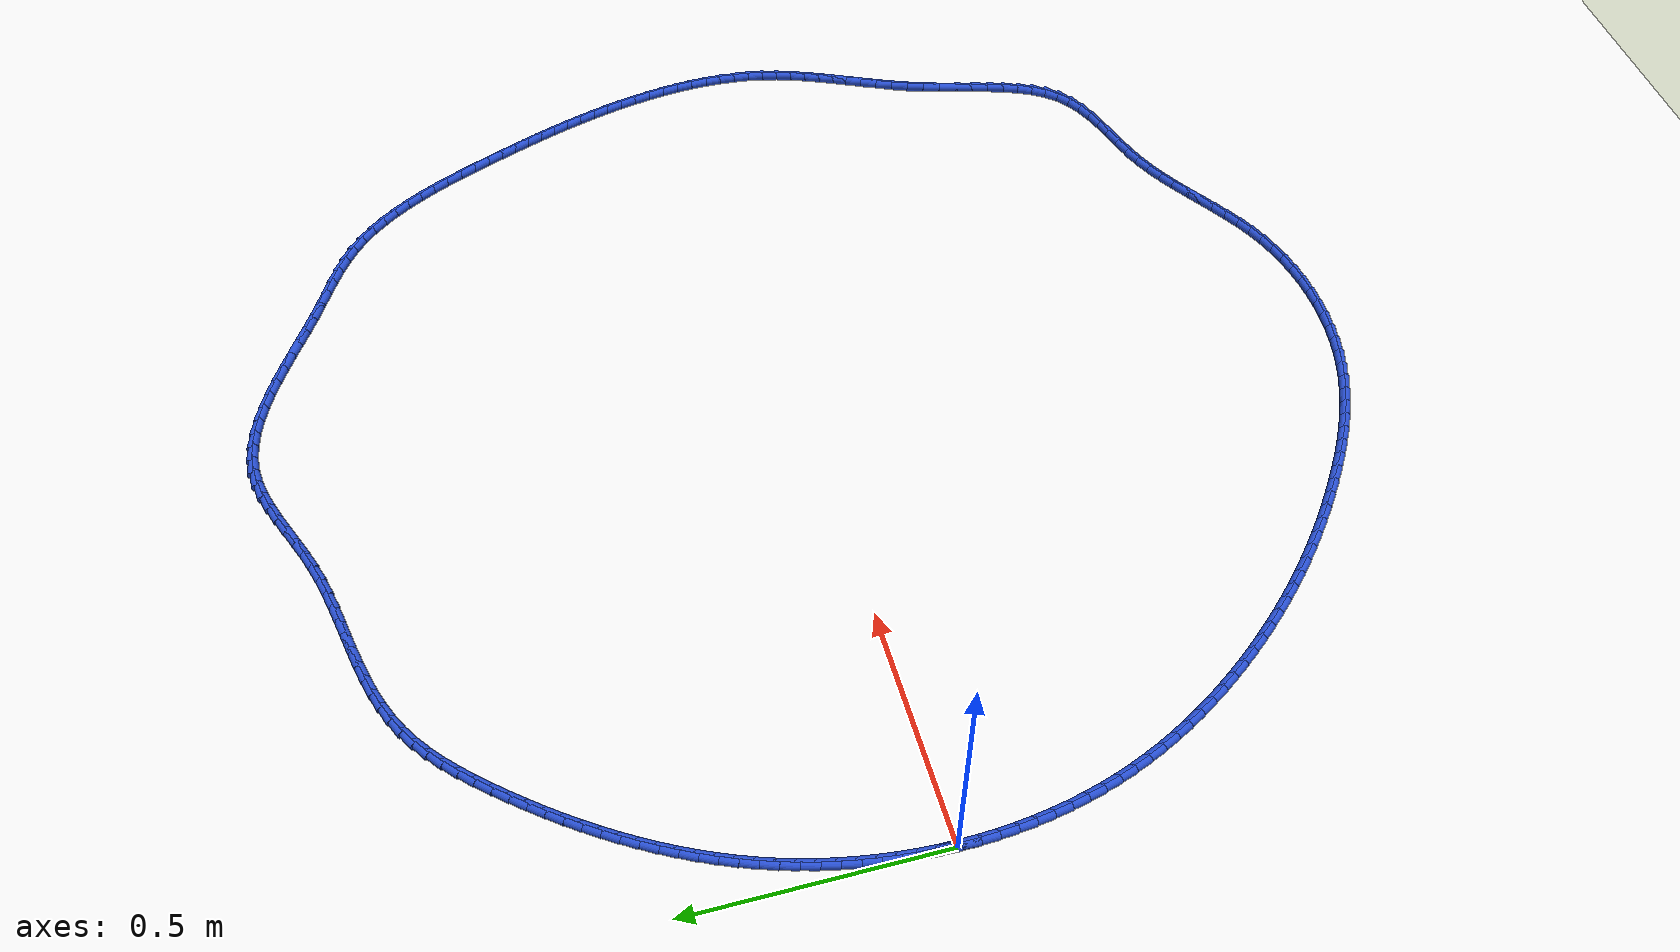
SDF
<sdf version="1.6">
 <world name="default">
  <light name="sun" type="directional">
   <pose>0 0 10 0 -0 0</pose>
   <diffuse>0.8 0.8 0.8 1</diffuse>
   <specular>0.2 0.2 0.2 1</specular>
   <attenuation>
    <range>1000</range>
    <constant>0.9</constant>
    <linear>0.01</linear>
    <quadratic>0.001</quadratic>
   </attenuation>
   <direction>-0.5 0.1 -0.9</direction>
  </light>
  <model name="ground_plane">
   <static>1</static>
   <link name="link">
    <collision name="collision">
     <geometry><plane><normal>0 0 1</normal><size>100 100</size></plane></geometry>
     <surface><friction><ode><mu>100</mu><mu2>50</mu2></ode></friction></surface>
    </collision>
    <visual name="visual">
     <cast_shadows>0</cast_shadows>
     <geometry><plane><normal>0 0 1</normal><size>100 100</size></plane></geometry>
     <material>
      <script><uri>file://media/materials/scripts/gazebo.material</uri><name>Gazebo/WhiteGlow</name></script>
     </material>
    </visual>
   </link>
  </model>
  <gravity>0 0 -9.8</gravity>
  <magnetic_field>6e-06 2.3e-05 -4.2e-05</magnetic_field>
  <atmosphere type="adiabatic"/>
  <physics name="default_physics" default="0" type="ode">
   <max_step_size>0.001</max_step_size>
   <real_time_factor>1</real_time_factor>
   <real_time_update_rate>1000</real_time_update_rate>
  </physics>
  <scene><ambient>0.4 0.4 0.4 1</ambient><background>0.7 0.7 0.7 1</background><shadows>1</shadows></scene>
  <spherical_coordinates>
   <surface_model>EARTH_WGS84</surface_model>
   <latitude_deg>0</latitude_deg>
   <longitude_deg>0</longitude_deg>
   <elevation>0</elevation>
   <heading_deg>0</heading_deg>
  </spherical_coordinates>
  <model name="line">
   <link name="link_0">
    <pose>2.2551405187698492e-17 4.85722573273506e-17 0.01 0 1.57 1.5520220317572857</pose>
    <collision name="collision">
     <geometry><cylinder><radius>0.01</radius><length>0.08</length></cylinder></geometry>
    </collision>
    <visual name="visual">
     <material>
      <script><name>Gazebo/Blue</name><uri>file://media/materials/scripts/gazebo.material</uri></script>
     </material>
     <geometry><cylinder><radius>0.01</radius><length>0.08</length></cylinder></geometry>
    </visual>
   </link>
   <link name="link_1">
    <pose>0.0006526197692008362 0.034757261931345186 0.01 0 1.57 1.5178676718023638</pose>
    <collision name="collision">
     <geometry><cylinder><radius>0.01</radius><length>0.08</length></cylinder></geometry>
    </collision>
    <visual name="visual">
     <material>
      <script><name>Gazebo/Blue</name><uri>file://media/materials/scripts/gazebo.material</uri></script>
     </material>
     <geometry><cylinder><radius>0.01</radius><length>0.08</length></cylinder></geometry>
    </visual>
   </link>
   <link name="link_2">
    <pose>0.002491596640277104 0.06946925844557372 0.01 0 1.57 1.4837287674956556</pose>
    <collision name="collision">
     <geometry><cylinder><radius>0.01</radius><length>0.08</length></cylinder></geometry>
    </collision>
    <visual name="visual">
     <material>
      <script><name>Gazebo/Blue</name><uri>file://media/materials/scripts/gazebo.material</uri></script>
     </material>
     <geometry><cylinder><radius>0.01</radius><length>0.08</length></cylinder></geometry>
    </visual>
   </link>
   <link name="link_3">
    <pose>0.005513291684226105 0.10408669374520456 0.01 0 1.57 1.4495392395560756</pose>
    <collision name="collision">
     <geometry><cylinder><radius>0.01</radius><length>0.08</length></cylinder></geometry>
    </collision>
    <visual name="visual">
     <material>
      <script><name>Gazebo/Blue</name><uri>file://media/materials/scripts/gazebo.material</uri></script>
     </material>
     <geometry><cylinder><radius>0.01</radius><length>0.08</length></cylinder></geometry>
    </visual>
   </link>
   <link name="link_4">
    <pose>0.009714065972045112 0.13856027203275648 0.01 0 1.57 1.415233017115805</pose>
    <collision name="collision">
     <geometry><cylinder><radius>0.01</radius><length>0.08</length></cylinder></geometry>
    </collision>
    <visual name="visual">
     <material>
      <script><name>Gazebo/Blue</name><uri>file://media/materials/scripts/gazebo.material</uri></script>
     </material>
     <geometry><cylinder><radius>0.01</radius><length>0.08</length></cylinder></geometry>
    </visual>
   </link>
   <link name="link_5">
    <pose>0.0150902805747314 0.17284069751074838 0.01 0 1.57 1.3807442603048132</pose>
    <collision name="collision">
     <geometry><cylinder><radius>0.01</radius><length>0.08</length></cylinder></geometry>
    </collision>
    <visual name="visual">
     <material>
      <script><name>Gazebo/Blue</name><uri>file://media/materials/scripts/gazebo.material</uri></script>
     </material>
     <geometry><cylinder><radius>0.01</radius><length>0.08</length></cylinder></geometry>
    </visual>
   </link>
   <link name="link_6">
    <pose>0.02163829656328225 0.2068786743816991 0.01 0 1.57 1.3460076059429122</pose>
    <collision name="collision">
     <geometry><cylinder><radius>0.01</radius><length>0.08</length></cylinder></geometry>
    </collision>
    <visual name="visual">
     <material>
      <script><name>Gazebo/Blue</name><uri>file://media/materials/scripts/gazebo.material</uri></script>
     </material>
     <geometry><cylinder><radius>0.01</radius><length>0.08</length></cylinder></geometry>
    </visual>
   </link>
   <link name="link_7">
    <pose>0.029354475008694918 0.24062490684812743 0.01 0 1.57 1.3109584502353298</pose>
    <collision name="collision">
     <geometry><cylinder><radius>0.01</radius><length>0.08</length></cylinder></geometry>
    </collision>
    <visual name="visual">
     <material>
      <script><name>Gazebo/Blue</name><uri>file://media/materials/scripts/gazebo.material</uri></script>
     </material>
     <geometry><cylinder><radius>0.01</radius><length>0.08</length></cylinder></geometry>
    </visual>
   </link>
   <link name="link_8">
    <pose>0.0382351769819667 0.2740300991125523 0.01 0 1.57 1.275533282397632</pose>
    <collision name="collision">
     <geometry><cylinder><radius>0.01</radius><length>0.08</length></cylinder></geometry>
    </collision>
    <visual name="visual">
     <material>
      <script><name>Gazebo/Blue</name><uri>file://media/materials/scripts/gazebo.material</uri></script>
     </material>
     <geometry><cylinder><radius>0.01</radius><length>0.08</length></cylinder></geometry>
    </visual>
   </link>
   <link name="link_9">
    <pose>0.04827676355409487 0.30704495537749243 0.01 0 1.57 1.2396948223564486</pose>
    <collision name="collision">
     <geometry><cylinder><radius>0.01</radius><length>0.08</length></cylinder></geometry>
    </collision>
    <visual name="visual">
     <material>
      <script><name>Gazebo/Blue</name><uri>file://media/materials/scripts/gazebo.material</uri></script>
     </material>
     <geometry><cylinder><radius>0.01</radius><length>0.08</length></cylinder></geometry>
    </visual>
   </link>
   <link name="link_10">
    <pose>0.059474993377184336 0.3396210488036305 0.01 0 1.57 1.204096763167114</pose>
    <collision name="collision">
     <geometry><cylinder><radius>0.01</radius><length>0.08</length></cylinder></geometry>
    </collision>
    <visual name="visual">
     <material>
      <script><name>Gazebo/Blue</name><uri>file://media/materials/scripts/gazebo.material</uri></script>
     </material>
     <geometry><cylinder><radius>0.01</radius><length>0.08</length></cylinder></geometry>
    </visual>
   </link>
   <link name="link_11">
    <pose>0.07180875730859781 0.3717342834750819 0.01 0 1.57 1.169546582591434</pose>
    <collision name="collision">
     <geometry><cylinder><radius>0.01</radius><length>0.08</length></cylinder></geometry>
    </collision>
    <visual name="visual">
     <material>
      <script><name>Gazebo/Blue</name><uri>file://media/materials/scripts/gazebo.material</uri></script>
     </material>
     <geometry><cylinder><radius>0.01</radius><length>0.08</length></cylinder></geometry>
    </visual>
   </link>
   <link name="link_12">
    <pose>0.08523821304139582 0.4033875850987203 0.01 0 1.57 1.1361345362943869</pose>
    <collision name="collision">
     <geometry><cylinder><radius>0.01</radius><length>0.08</length></cylinder></geometry>
    </collision>
    <visual name="visual">
     <material>
      <script><name>Gazebo/Blue</name><uri>file://media/materials/scripts/gazebo.material</uri></script>
     </material>
     <geometry><cylinder><radius>0.01</radius><length>0.08</length></cylinder></geometry>
    </visual>
   </link>
   <link name="link_13">
    <pose>0.09972254148869569 0.43458528833608023 0.01 0 1.57 1.1038973909347334</pose>
    <collision name="collision">
     <geometry><cylinder><radius>0.01</radius><length>0.08</length></cylinder></geometry>
    </collision>
    <visual name="visual">
     <material>
      <script><name>Gazebo/Blue</name><uri>file://media/materials/scripts/gazebo.material</uri></script>
     </material>
     <geometry><cylinder><radius>0.01</radius><length>0.08</length></cylinder></geometry>
    </visual>
   </link>
   <link name="link_14">
    <pose>0.11522092356361464 0.4653317278486957 0.01 0 1.57 1.0728595686364584</pose>
    <collision name="collision">
     <geometry><cylinder><radius>0.01</radius><length>0.08</length></cylinder></geometry>
    </collision>
    <visual name="visual">
     <material>
      <script><name>Gazebo/Blue</name><uri>file://media/materials/scripts/gazebo.material</uri></script>
     </material>
     <geometry><cylinder><radius>0.01</radius><length>0.08</length></cylinder></geometry>
    </visual>
   </link>
   <link name="link_15">
    <pose>0.13169254017926996 0.4956312382981011 0.01 0 1.57 1.0430343632465913</pose>
    <collision name="collision">
     <geometry><cylinder><radius>0.01</radius><length>0.08</length></cylinder></geometry>
    </collision>
    <visual name="visual">
     <material>
      <script><name>Gazebo/Blue</name><uri>file://media/materials/scripts/gazebo.material</uri></script>
     </material>
     <geometry><cylinder><radius>0.01</radius><length>0.08</length></cylinder></geometry>
    </visual>
   </link>
   <link name="link_16">
    <pose>0.14909657224877892 0.5254881543458305 0.01 0 1.57 1.0144252605430866</pose>
    <collision name="collision">
     <geometry><cylinder><radius>0.01</radius><length>0.08</length></cylinder></geometry>
    </collision>
    <visual name="visual">
     <material>
      <script><name>Gazebo/Blue</name><uri>file://media/materials/scripts/gazebo.material</uri></script>
     </material>
     <geometry><cylinder><radius>0.01</radius><length>0.08</length></cylinder></geometry>
    </visual>
   </link>
   <link name="link_17">
    <pose>0.16739220068525873 0.5549068106534183 0.01 0 1.57 0.9870272946597509</pose>
    <collision name="collision">
     <geometry><cylinder><radius>0.01</radius><length>0.08</length></cylinder></geometry>
    </collision>
    <visual name="visual">
     <material>
      <script><name>Gazebo/Blue</name><uri>file://media/materials/scripts/gazebo.material</uri></script>
     </material>
     <geometry><cylinder><radius>0.01</radius><length>0.08</length></cylinder></geometry>
    </visual>
   </link>
   <link name="link_18">
    <pose>0.18653860640182668 0.5838915418823983 0.01 0 1.57 0.9608283861322301</pose>
    <collision name="collision">
     <geometry><cylinder><radius>0.01</radius><length>0.08</length></cylinder></geometry>
    </collision>
    <visual name="visual">
     <material>
      <script><name>Gazebo/Blue</name><uri>file://media/materials/scripts/gazebo.material</uri></script>
     </material>
     <geometry><cylinder><radius>0.01</radius><length>0.08</length></cylinder></geometry>
    </visual>
   </link>
   <link name="link_19">
    <pose>0.20649497031160002 0.6124466826943054 0.01 0 1.57 0.9358106203439434</pose>
    <collision name="collision">
     <geometry><cylinder><radius>0.01</radius><length>0.08</length></cylinder></geometry>
    </collision>
    <visual name="visual">
     <material>
      <script><name>Gazebo/Blue</name><uri>file://media/materials/scripts/gazebo.material</uri></script>
     </material>
     <geometry><cylinder><radius>0.01</radius><length>0.08</length></cylinder></geometry>
    </visual>
   </link>
   <link name="link_20">
    <pose>0.22722047332769596 0.6405765677506731 0.01 0 1.57 0.9119514376425432</pose>
    <collision name="collision">
     <geometry><cylinder><radius>0.01</radius><length>0.08</length></cylinder></geometry>
    </collision>
    <visual name="visual">
     <material>
      <script><name>Gazebo/Blue</name><uri>file://media/materials/scripts/gazebo.material</uri></script>
     </material>
     <geometry><cylinder><radius>0.01</radius><length>0.08</length></cylinder></geometry>
    </visual>
   </link>
   <link name="link_21">
    <pose>0.24867429636323188 0.6682855317130362 0.01 0 1.57 0.8892247173132739</pose>
    <collision name="collision">
     <geometry><cylinder><radius>0.01</radius><length>0.08</length></cylinder></geometry>
    </collision>
    <visual name="visual">
     <material>
      <script><name>Gazebo/Blue</name><uri>file://media/materials/scripts/gazebo.material</uri></script>
     </material>
     <geometry><cylinder><radius>0.01</radius><length>0.08</length></cylinder></geometry>
    </visual>
   </link>
   <link name="link_22">
    <pose>0.27081562033132495 0.6955779092429286 0.01 0 1.57 0.8676017466082129</pose>
    <collision name="collision">
     <geometry><cylinder><radius>0.01</radius><length>0.08</length></cylinder></geometry>
    </collision>
    <visual name="visual">
     <material>
      <script><name>Gazebo/Blue</name><uri>file://media/materials/scripts/gazebo.material</uri></script>
     </material>
     <geometry><cylinder><radius>0.01</radius><length>0.08</length></cylinder></geometry>
    </visual>
   </link>
   <link name="link_23">
    <pose>0.29360362614509244 0.7224580350018847 0.01 0 1.57 0.8469890773231284</pose>
    <collision name="collision">
     <geometry><cylinder><radius>0.01</radius><length>0.08</length></cylinder></geometry>
    </collision>
    <visual name="visual">
     <material>
      <script><name>Gazebo/Blue</name><uri>file://media/materials/scripts/gazebo.material</uri></script>
     </material>
     <geometry><cylinder><radius>0.01</radius><length>0.08</length></cylinder></geometry>
    </visual>
   </link>
   <link name="link_24">
    <pose>0.3169983939395713 0.7489279005185449 0.01 0 1.57 0.8236798708171605</pose>
    <collision name="collision">
     <geometry><cylinder><radius>0.01</radius><length>0.08</length></cylinder></geometry>
    </collision>
    <visual name="visual">
     <material>
      <script><name>Gazebo/Blue</name><uri>file://media/materials/scripts/gazebo.material</uri></script>
     </material>
     <geometry><cylinder><radius>0.01</radius><length>0.08</length></cylinder></geometry>
    </visual>
   </link>
   <link name="link_25">
    <pose>0.34101194092581316 0.7748541631303625 0.01 0 1.57 0.7918041883691699</pose>
    <collision name="collision">
     <geometry><cylinder><radius>0.01</radius><length>0.08</length></cylinder></geometry>
    </collision>
    <visual name="visual">
     <material>
      <script><name>Gazebo/Blue</name><uri>file://media/materials/scripts/gazebo.material</uri></script>
     </material>
     <geometry><cylinder><radius>0.01</radius><length>0.08</length></cylinder></geometry>
    </visual>
   </link>
   <link name="link_26">
    <pose>0.36573564836350747 0.7998966785957256 0.01 0 1.57 0.7503292635145157</pose>
    <collision name="collision">
     <geometry><cylinder><radius>0.01</radius><length>0.08</length></cylinder></geometry>
    </collision>
    <visual name="visual">
     <material>
      <script><name>Gazebo/Blue</name><uri>file://media/materials/scripts/gazebo.material</uri></script>
     </material>
     <geometry><cylinder><radius>0.01</radius><length>0.08</length></cylinder></geometry>
    </visual>
   </link>
   <link name="link_27">
    <pose>0.3912675931842261 0.8236978555349047 0.01 0 1.57 0.6985291775158372</pose>
    <collision name="collision">
     <geometry><cylinder><radius>0.01</radius><length>0.08</length></cylinder></geometry>
    </collision>
    <visual name="visual">
     <material>
      <script><name>Gazebo/Blue</name><uri>file://media/materials/scripts/gazebo.material</uri></script>
     </material>
     <geometry><cylinder><radius>0.01</radius><length>0.08</length></cylinder></geometry>
    </visual>
   </link>
   <link name="link_28">
    <pose>0.41770585231954077 0.8459001025681697 0.01 0 1.57 0.6356127868367223</pose>
    <collision name="collision">
     <geometry><cylinder><radius>0.01</radius><length>0.08</length></cylinder></geometry>
    </collision>
    <visual name="visual">
     <material>
      <script><name>Gazebo/Blue</name><uri>file://media/materials/scripts/gazebo.material</uri></script>
     </material>
     <geometry><cylinder><radius>0.01</radius><length>0.08</length></cylinder></geometry>
    </visual>
   </link>
   <link name="link_29">
    <pose>0.44514850270102396 0.8661458283157916 0.01 0 1.57 0.5608863188310123</pose>
    <collision name="collision">
     <geometry><cylinder><radius>0.01</radius><length>0.08</length></cylinder></geometry>
    </collision>
    <visual name="visual">
     <material>
      <script><name>Gazebo/Blue</name><uri>file://media/materials/scripts/gazebo.material</uri></script>
     </material>
     <geometry><cylinder><radius>0.01</radius><length>0.08</length></cylinder></geometry>
    </visual>
   </link>
   <link name="link_30">
    <pose>0.47369362126024706 0.8840774413980399 0.01 0 1.57 0.4772093467098694</pose>
    <collision name="collision">
     <geometry><cylinder><radius>0.01</radius><length>0.08</length></cylinder></geometry>
    </collision>
    <visual name="visual">
     <material>
      <script><name>Gazebo/Blue</name><uri>file://media/materials/scripts/gazebo.material</uri></script>
     </material>
     <geometry><cylinder><radius>0.01</radius><length>0.08</length></cylinder></geometry>
    </visual>
   </link>
   <link name="link_31">
    <pose>0.5034063994888788 0.8994409967645567 0.01 0 1.57 0.4002779082120154</pose>
    <collision name="collision">
     <geometry><cylinder><radius>0.01</radius><length>0.08</length></cylinder></geometry>
    </collision>
    <visual name="visual">
     <material>
      <script><name>Gazebo/Blue</name><uri>file://media/materials/scripts/gazebo.material</uri></script>
     </material>
     <geometry><cylinder><radius>0.01</radius><length>0.08</length></cylinder></geometry>
    </visual>
   </link>
   <link name="link_32">
    <pose>0.5341975645971737 0.9124693804925118 0.01 0 1.57 0.33559839236085703</pose>
    <collision name="collision">
     <geometry><cylinder><radius>0.01</radius><length>0.08</length></cylinder></geometry>
    </collision>
    <visual name="visual">
     <material>
      <script><name>Gazebo/Blue</name><uri>file://media/materials/scripts/gazebo.material</uri></script>
     </material>
     <geometry><cylinder><radius>0.01</radius><length>0.08</length></cylinder></geometry>
    </visual>
   </link>
   <link name="link_33">
    <pose>0.5659325323236241 0.9235382885998973 0.01 0 1.57 0.2835985488227313</pose>
    <collision name="collision">
     <geometry><cylinder><radius>0.01</radius><length>0.08</length></cylinder></geometry>
    </collision>
    <visual name="visual">
     <material>
      <script><name>Gazebo/Blue</name><uri>file://media/materials/scripts/gazebo.material</uri></script>
     </material>
     <geometry><cylinder><radius>0.01</radius><length>0.08</length></cylinder></geometry>
    </visual>
   </link>
   <link name="link_34">
    <pose>0.598476712482685 0.9330234357757281 0.01 0 1.57 0.24419653883842143</pose>
    <collision name="collision">
     <geometry><cylinder><radius>0.01</radius><length>0.08</length></cylinder></geometry>
    </collision>
    <visual name="visual">
     <material>
      <script><name>Gazebo/Blue</name><uri>file://media/materials/scripts/gazebo.material</uri></script>
     </material>
     <geometry><cylinder><radius>0.01</radius><length>0.08</length></cylinder></geometry>
    </visual>
   </link>
   <link name="link_35">
    <pose>0.6316955148888105 0.9413005367090175 0.01 0 1.57 0.21705390569500263</pose>
    <collision name="collision">
     <geometry><cylinder><radius>0.01</radius><length>0.08</length></cylinder></geometry>
    </collision>
    <visual name="visual">
     <material>
      <script><name>Gazebo/Blue</name><uri>file://media/materials/scripts/gazebo.material</uri></script>
     </material>
     <geometry><cylinder><radius>0.01</radius><length>0.08</length></cylinder></geometry>
    </visual>
   </link>
   <link name="link_36">
    <pose>0.6654543493564564 0.9487453060887807 0.01 0 1.57 0.2017624870796014</pose>
    <collision name="collision">
     <geometry><cylinder><radius>0.01</radius><length>0.08</length></cylinder></geometry>
    </collision>
    <visual name="visual">
     <material>
      <script><name>Gazebo/Blue</name><uri>file://media/materials/scripts/gazebo.material</uri></script>
     </material>
     <geometry><cylinder><radius>0.01</radius><length>0.08</length></cylinder></geometry>
    </visual>
   </link>
   <link name="link_37">
    <pose>0.6996186257000767 0.9557334586040311 0.01 0 1.57 0.19796023497700035</pose>
    <collision name="collision">
     <geometry><cylinder><radius>0.01</radius><length>0.08</length></cylinder></geometry>
    </collision>
    <visual name="visual">
     <material>
      <script><name>Gazebo/Blue</name><uri>file://media/materials/scripts/gazebo.material</uri></script>
     </material>
     <geometry><cylinder><radius>0.01</radius><length>0.08</length></cylinder></geometry>
    </visual>
   </link>
   <link name="link_38">
    <pose>0.7340537537341263 0.9626407089437834 0.01 0 1.57 0.20538679612878377</pose>
    <collision name="collision">
     <geometry><cylinder><radius>0.01</radius><length>0.08</length></cylinder></geometry>
    </collision>
    <visual name="visual">
     <material>
      <script><name>Gazebo/Blue</name><uri>file://media/materials/scripts/gazebo.material</uri></script>
     </material>
     <geometry><cylinder><radius>0.01</radius><length>0.08</length></cylinder></geometry>
    </visual>
   </link>
   <link name="link_39">
    <pose>0.7686251432730602 0.9698427717970516 0.01 0 1.57 0.22389121268520118</pose>
    <collision name="collision">
     <geometry><cylinder><radius>0.01</radius><length>0.08</length></cylinder></geometry>
    </collision>
    <visual name="visual">
     <material>
      <script><name>Gazebo/Blue</name><uri>file://media/materials/scripts/gazebo.material</uri></script>
     </material>
     <geometry><cylinder><radius>0.01</radius><length>0.08</length></cylinder></geometry>
    </visual>
   </link>
   <link name="link_40">
    <pose>0.8031982041313327 0.97771536185285 0.01 0 1.57 0.25339945433759176</pose>
    <collision name="collision">
     <geometry><cylinder><radius>0.01</radius><length>0.08</length></cylinder></geometry>
    </collision>
    <visual name="visual">
     <material>
      <script><name>Gazebo/Blue</name><uri>file://media/materials/scripts/gazebo.material</uri></script>
     </material>
     <geometry><cylinder><radius>0.01</radius><length>0.08</length></cylinder></geometry>
    </visual>
   </link>
   <link name="link_41">
    <pose>0.8376383461233992 0.9866341938001926 0.01 0 1.57 0.2938444212592218</pose>
    <collision name="collision">
     <geometry><cylinder><radius>0.01</radius><length>0.08</length></cylinder></geometry>
    </collision>
    <visual name="visual">
     <material>
      <script><name>Gazebo/Blue</name><uri>file://media/materials/scripts/gazebo.material</uri></script>
     </material>
     <geometry><cylinder><radius>0.01</radius><length>0.08</length></cylinder></geometry>
    </visual>
   </link>
   <link name="link_42">
    <pose>0.8718109790637136 0.9969749823280936 0.01 0 1.57 0.341421814520982</pose>
    <collision name="collision">
     <geometry><cylinder><radius>0.01</radius><length>0.08</length></cylinder></geometry>
    </collision>
    <visual name="visual">
     <material>
      <script><name>Gazebo/Blue</name><uri>file://media/materials/scripts/gazebo.material</uri></script>
     </material>
     <geometry><cylinder><radius>0.01</radius><length>0.08</length></cylinder></geometry>
    </visual>
   </link>
   <link name="link_43">
    <pose>0.9056024920562179 1.008982371033478 0.01 0 1.57 0.3754263664348554</pose>
    <collision name="collision">
     <geometry><cylinder><radius>0.01</radius><length>0.08</length></cylinder></geometry>
    </collision>
    <visual name="visual">
     <material>
      <script><name>Gazebo/Blue</name><uri>file://media/materials/scripts/gazebo.material</uri></script>
     </material>
     <geometry><cylinder><radius>0.01</radius><length>0.08</length></cylinder></geometry>
    </visual>
   </link>
   <link name="link_44">
    <pose>0.9390190820503159 1.022152486974797 0.01 0 1.57 0.38901049553964784</pose>
    <collision name="collision">
     <geometry><cylinder><radius>0.01</radius><length>0.08</length></cylinder></geometry>
    </collision>
    <visual name="visual">
     <material>
      <script><name>Gazebo/Blue</name><uri>file://media/materials/scripts/gazebo.material</uri></script>
     </material>
     <geometry><cylinder><radius>0.01</radius><length>0.08</length></cylinder></geometry>
    </visual>
   </link>
   <link name="link_45">
    <pose>0.9721094082465269 1.0357161682630451 0.01 0 1.57 0.3821516387229275</pose>
    <collision name="collision">
     <geometry><cylinder><radius>0.01</radius><length>0.08</length></cylinder></geometry>
    </collision>
    <visual name="visual">
     <material>
      <script><name>Gazebo/Blue</name><uri>file://media/materials/scripts/gazebo.material</uri></script>
     </material>
     <geometry><cylinder><radius>0.01</radius><length>0.08</length></cylinder></geometry>
    </visual>
   </link>
   <link name="link_46">
    <pose>1.0049221797159988 1.0489039414353825 0.01 0 1.57 0.3540110989152577</pose>
    <collision name="collision">
     <geometry><cylinder><radius>0.01</radius><length>0.08</length></cylinder></geometry>
    </collision>
    <visual name="visual">
     <material>
      <script><name>Gazebo/Blue</name><uri>file://media/materials/scripts/gazebo.material</uri></script>
     </material>
     <geometry><cylinder><radius>0.01</radius><length>0.08</length></cylinder></geometry>
    </visual>
   </link>
   <link name="link_47">
    <pose>1.0375061055298784 1.060946333028968 0.01 0 1.57 0.3029228911283183</pose>
    <collision name="collision">
     <geometry><cylinder><radius>0.01</radius><length>0.08</length></cylinder></geometry>
    </collision>
    <visual name="visual">
     <material>
      <script><name>Gazebo/Blue</name><uri>file://media/materials/scripts/gazebo.material</uri></script>
     </material>
     <geometry><cylinder><radius>0.01</radius><length>0.08</length></cylinder></geometry>
    </visual>
   </link>
   <link name="link_48">
    <pose>1.0699098947593138 1.07107386958096 0.01 0 1.57 0.22667351596766108</pose>
    <collision name="collision">
     <geometry><cylinder><radius>0.01</radius><length>0.08</length></cylinder></geometry>
    </collision>
    <visual name="visual">
     <material>
      <script><name>Gazebo/Blue</name><uri>file://media/materials/scripts/gazebo.material</uri></script>
     </material>
     <geometry><cylinder><radius>0.01</radius><length>0.08</length></cylinder></geometry>
    </visual>
   </link>
   <link name="link_49">
    <pose>1.1021822564754513 1.0785170776285191 0.01 0 1.57 0.12330573929465422</pose>
    <collision name="collision">
     <geometry><cylinder><radius>0.01</radius><length>0.08</length></cylinder></geometry>
    </collision>
    <visual name="visual">
     <material>
      <script><name>Gazebo/Blue</name><uri>file://media/materials/scripts/gazebo.material</uri></script>
     </material>
     <geometry><cylinder><radius>0.01</radius><length>0.08</length></cylinder></geometry>
    </visual>
   </link>
   <link name="link_50">
    <pose>1.134371899709255 1.0825064846296502 0.01 0 1.57 -0.0007828287084345316</pose>
    <collision name="collision">
     <geometry><cylinder><radius>0.01</radius><length>0.08</length></cylinder></geometry>
    </collision>
    <visual name="visual">
     <material>
      <script><name>Gazebo/Blue</name><uri>file://media/materials/scripts/gazebo.material</uri></script>
     </material>
     <geometry><cylinder><radius>0.01</radius><length>0.08</length></cylinder></geometry>
    </visual>
   </link>
   <link name="link_51">
    <pose>1.166518426157476 1.0824813194007294 0.01 0 1.57 -0.11799859188616538</pose>
    <collision name="collision">
     <geometry><cylinder><radius>0.01</radius><length>0.08</length></cylinder></geometry>
    </collision>
    <visual name="visual">
     <material>
      <script><name>Gazebo/Blue</name><uri>file://media/materials/scripts/gazebo.material</uri></script>
     </material>
     <geometry><cylinder><radius>0.01</radius><length>0.08</length></cylinder></geometry>
    </visual>
   </link>
   <link name="link_52">
    <pose>1.1986267851600196 1.078674895368984 0.01 0 1.57 -0.2198442127290294</pose>
    <collision name="collision">
     <geometry><cylinder><radius>0.01</radius><length>0.08</length></cylinder></geometry>
    </collision>
    <visual name="visual">
     <material>
      <script><name>Gazebo/Blue</name><uri>file://media/materials/scripts/gazebo.material</uri></script>
     </material>
     <geometry><cylinder><radius>0.01</radius><length>0.08</length></cylinder></geometry>
    </visual>
   </link>
   <link name="link_53">
    <pose>1.2306936857451294 1.071509358851439 0.01 0 1.57 -0.3056018217969712</pose>
    <collision name="collision">
     <geometry><cylinder><radius>0.01</radius><length>0.08</length></cylinder></geometry>
    </collision>
    <visual name="visual">
     <material>
      <script><name>Gazebo/Blue</name><uri>file://media/materials/scripts/gazebo.material</uri></script>
     </material>
     <geometry><cylinder><radius>0.01</radius><length>0.08</length></cylinder></geometry>
    </visual>
   </link>
   <link name="link_54">
    <pose>1.262715836941046 1.0614068561651182 0.01 0 1.57 -0.37585171176238286</pose>
    <collision name="collision">
     <geometry><cylinder><radius>0.01</radius><length>0.08</length></cylinder></geometry>
    </collision>
    <visual name="visual">
     <material>
      <script><name>Gazebo/Blue</name><uri>file://media/materials/scripts/gazebo.material</uri></script>
     </material>
     <geometry><cylinder><radius>0.01</radius><length>0.08</length></cylinder></geometry>
    </visual>
   </link>
   <link name="link_55">
    <pose>1.2946899477760132 1.048789533627047 0.01 0 1.57 -0.43179828862515046</pose>
    <collision name="collision">
     <geometry><cylinder><radius>0.01</radius><length>0.08</length></cylinder></geometry>
    </collision>
    <visual name="visual">
     <material>
      <script><name>Gazebo/Blue</name><uri>file://media/materials/scripts/gazebo.material</uri></script>
     </material>
     <geometry><cylinder><radius>0.01</radius><length>0.08</length></cylinder></geometry>
    </visual>
   </link>
   <link name="link_56">
    <pose>1.3266127272782724 1.0340795375542498 0.01 0 1.57 -0.4747919881837959</pose>
    <collision name="collision">
     <geometry><cylinder><radius>0.01</radius><length>0.08</length></cylinder></geometry>
    </collision>
    <visual name="visual">
     <material>
      <script><name>Gazebo/Blue</name><uri>file://media/materials/scripts/gazebo.material</uri></script>
     </material>
     <geometry><cylinder><radius>0.01</radius><length>0.08</length></cylinder></geometry>
    </visual>
   </link>
   <link name="link_57">
    <pose>1.3584808844760656 1.0176990142637505 0.01 0 1.57 -0.5060540508756706</pose>
    <collision name="collision">
     <geometry><cylinder><radius>0.01</radius><length>0.08</length></cylinder></geometry>
    </collision>
    <visual name="visual">
     <material>
      <script><name>Gazebo/Blue</name><uri>file://media/materials/scripts/gazebo.material</uri></script>
     </material>
     <geometry><cylinder><radius>0.01</radius><length>0.08</length></cylinder></geometry>
    </visual>
   </link>
   <link name="link_58">
    <pose>1.3902911283976356 1.0000701100725744 0.01 0 1.57 -0.5265424003015073</pose>
    <collision name="collision">
     <geometry><cylinder><radius>0.01</radius><length>0.08</length></cylinder></geometry>
    </collision>
    <visual name="visual">
     <material>
      <script><name>Gazebo/Blue</name><uri>file://media/materials/scripts/gazebo.material</uri></script>
     </material>
     <geometry><cylinder><radius>0.01</radius><length>0.08</length></cylinder></geometry>
    </visual>
   </link>
   <link name="link_59">
    <pose>1.4220401680712238 0.981614971297746 0.01 0 1.57 -0.5368962742300613</pose>
    <collision name="collision">
     <geometry><cylinder><radius>0.01</radius><length>0.08</length></cylinder></geometry>
    </collision>
    <visual name="visual">
     <material>
      <script><name>Gazebo/Blue</name><uri>file://media/materials/scripts/gazebo.material</uri></script>
     </material>
     <geometry><cylinder><radius>0.01</radius><length>0.08</length></cylinder></geometry>
    </visual>
   </link>
   <link name="link_60">
    <pose>1.4537247125250734 0.9627557442562897 0.01 0 1.57 -0.5374166765083981</pose>
    <collision name="collision">
     <geometry><cylinder><radius>0.01</radius><length>0.08</length></cylinder></geometry>
    </collision>
    <visual name="visual">
     <material>
      <script><name>Gazebo/Blue</name><uri>file://media/materials/scripts/gazebo.material</uri></script>
     </material>
     <geometry><cylinder><radius>0.01</radius><length>0.08</length></cylinder></geometry>
    </visual>
   </link>
   <link name="link_61">
    <pose>1.4853414707874262 0.9439145752652301 0.01 0 1.57 -0.5280583015248342</pose>
    <collision name="collision">
     <geometry><cylinder><radius>0.01</radius><length>0.08</length></cylinder></geometry>
    </collision>
    <visual name="visual">
     <material>
      <script><name>Gazebo/Blue</name><uri>file://media/materials/scripts/gazebo.material</uri></script>
     </material>
     <geometry><cylinder><radius>0.01</radius><length>0.08</length></cylinder></geometry>
    </visual>
   </link>
   <link name="link_62">
    <pose>1.516887151886524 0.9255136106415917 0.01 0 1.57 -0.5090978315281874</pose>
    <collision name="collision">
     <geometry><cylinder><radius>0.01</radius><length>0.08</length></cylinder></geometry>
    </collision>
    <visual name="visual">
     <material>
      <script><name>Gazebo/Blue</name><uri>file://media/materials/scripts/gazebo.material</uri></script>
     </material>
     <geometry><cylinder><radius>0.01</radius><length>0.08</length></cylinder></geometry>
    </visual>
   </link>
   <link name="link_63">
    <pose>1.5483509427278555 0.9079513132214374 0.01 0 1.57 -0.49466513685424995</pose>
    <collision name="collision">
     <geometry><cylinder><radius>0.01</radius><length>0.08</length></cylinder></geometry>
    </collision>
    <visual name="visual">
     <material>
      <script><name>Gazebo/Blue</name><uri>file://media/materials/scripts/gazebo.material</uri></script>
     </material>
     <geometry><cylinder><radius>0.01</radius><length>0.08</length></cylinder></geometry>
    </visual>
   </link>
   <link name="link_64">
    <pose>1.5795603512828413 0.8911170980517203 0.01 0 1.57 -0.49937479113405114</pose>
    <collision name="collision">
     <geometry><cylinder><radius>0.01</radius><length>0.08</length></cylinder></geometry>
    </collision>
    <visual name="visual">
     <material>
      <script><name>Gazebo/Blue</name><uri>file://media/materials/scripts/gazebo.material</uri></script>
     </material>
     <geometry><cylinder><radius>0.01</radius><length>0.08</length></cylinder></geometry>
    </visual>
   </link>
   <link name="link_65">
    <pose>1.6101872611885775 0.8744103953599432 0.01 0 1.57 -0.5247733841061434</pose>
    <collision name="collision">
     <geometry><cylinder><radius>0.01</radius><length>0.08</length></cylinder></geometry>
    </collision>
    <visual name="visual">
     <material>
      <script><name>Gazebo/Blue</name><uri>file://media/materials/scripts/gazebo.material</uri></script>
     </material>
     <geometry><cylinder><radius>0.01</radius><length>0.08</length></cylinder></geometry>
    </visual>
   </link>
   <link name="link_66">
    <pose>1.6398972454323693 0.857210766227747 0.01 0 1.57 -0.5717888677509159</pose>
    <collision name="collision">
     <geometry><cylinder><radius>0.01</radius><length>0.08</length></cylinder></geometry>
    </collision>
    <visual name="visual">
     <material>
      <script><name>Gazebo/Blue</name><uri>file://media/materials/scripts/gazebo.material</uri></script>
     </material>
     <geometry><cylinder><radius>0.01</radius><length>0.08</length></cylinder></geometry>
    </visual>
   </link>
   <link name="link_67">
    <pose>1.6683558770015217 0.8388977717367696 0.01 0 1.57 -0.640927763032633</pose>
    <collision name="collision">
     <geometry><cylinder><radius>0.01</radius><length>0.08</length></cylinder></geometry>
    </collision>
    <visual name="visual">
     <material>
      <script><name>Gazebo/Blue</name><uri>file://media/materials/scripts/gazebo.material</uri></script>
     </material>
     <geometry><cylinder><radius>0.01</radius><length>0.08</length></cylinder></geometry>
    </visual>
   </link>
   <link name="link_68">
    <pose>1.695228730346821 0.8188509756124451 0.01 0 1.57 -0.7264622116394904</pose>
    <collision name="collision">
     <geometry><cylinder><radius>0.01</radius><length>0.08</length></cylinder></geometry>
    </collision>
    <visual name="visual">
     <material>
      <script><name>Gazebo/Blue</name><uri>file://media/materials/scripts/gazebo.material</uri></script>
     </material>
     <geometry><cylinder><radius>0.01</radius><length>0.08</length></cylinder></geometry>
    </visual>
   </link>
   <link name="link_69">
    <pose>1.7202663295713028 0.7966034040195507 0.01 0 1.57 -0.8081109301042511</pose>
    <collision name="collision">
     <geometry><cylinder><radius>0.01</radius><length>0.08</length></cylinder></geometry>
    </collision>
    <visual name="visual">
     <material>
      <script><name>Gazebo/Blue</name><uri>file://media/materials/scripts/gazebo.material</uri></script>
     </material>
     <geometry><cylinder><radius>0.01</radius><length>0.08</length></cylinder></geometry>
    </visual>
   </link>
   <link name="link_70">
    <pose>1.7435330389004884 0.7722550386016166 0.01 0 1.57 -0.8809381319537464</pose>
    <collision name="collision">
     <geometry><cylinder><radius>0.01</radius><length>0.08</length></cylinder></geometry>
    </collision>
    <visual name="visual">
     <material>
      <script><name>Gazebo/Blue</name><uri>file://media/materials/scripts/gazebo.material</uri></script>
     </material>
     <geometry><cylinder><radius>0.01</radius><length>0.08</length></cylinder></geometry>
    </visual>
   </link>
   <link name="link_71">
    <pose>1.7651656817415344 0.7460367592751173 0.01 0 1.57 -0.9449285223393277</pose>
    <collision name="collision">
     <geometry><cylinder><radius>0.01</radius><length>0.08</length></cylinder></geometry>
    </collision>
    <visual name="visual">
     <material>
      <script><name>Gazebo/Blue</name><uri>file://media/materials/scripts/gazebo.material</uri></script>
     </material>
     <geometry><cylinder><radius>0.01</radius><length>0.08</length></cylinder></geometry>
    </visual>
   </link>
   <link name="link_72">
    <pose>1.7853010815016 0.7181794459565285 0.01 0 1.57 -1.0003910972374062</pose>
    <collision name="collision">
     <geometry><cylinder><radius>0.01</radius><length>0.08</length></cylinder></geometry>
    </collision>
    <visual name="visual">
     <material>
      <script><name>Gazebo/Blue</name><uri>file://media/materials/scripts/gazebo.material</uri></script>
     </material>
     <geometry><cylinder><radius>0.01</radius><length>0.08</length></cylinder></geometry>
    </visual>
   </link>
   <link name="link_73">
    <pose>1.8040760615878415 0.6889139785623251 0.01 0 1.57 -1.0478073004338053</pose>
    <collision name="collision">
     <geometry><cylinder><radius>0.01</radius><length>0.08</length></cylinder></geometry>
    </collision>
    <visual name="visual">
     <material>
      <script><name>Gazebo/Blue</name><uri>file://media/materials/scripts/gazebo.material</uri></script>
     </material>
     <geometry><cylinder><radius>0.01</radius><length>0.08</length></cylinder></geometry>
    </visual>
   </link>
   <link name="link_74">
    <pose>1.821627445407416 0.6584712370089815 0.01 0 1.57 -1.0877161553787427</pose>
    <collision name="collision">
     <geometry><cylinder><radius>0.01</radius><length>0.08</length></cylinder></geometry>
    </collision>
    <visual name="visual">
     <material>
      <script><name>Gazebo/Blue</name><uri>file://media/materials/scripts/gazebo.material</uri></script>
     </material>
     <geometry><cylinder><radius>0.01</radius><length>0.08</length></cylinder></geometry>
    </visual>
   </link>
   <link name="link_75">
    <pose>1.8380920563674807 0.6270821012129728 0.01 0 1.57 -1.1206360292493904</pose>
    <collision name="collision">
     <geometry><cylinder><radius>0.01</radius><length>0.08</length></cylinder></geometry>
    </collision>
    <visual name="visual">
     <material>
      <script><name>Gazebo/Blue</name><uri>file://media/materials/scripts/gazebo.material</uri></script>
     </material>
     <geometry><cylinder><radius>0.01</radius><length>0.08</length></cylinder></geometry>
    </visual>
   </link>
   <link name="link_76">
    <pose>1.8536067178751936 0.5949774510907748 0.01 0 1.57 -1.1470150333500257</pose>
    <collision name="collision">
     <geometry><cylinder><radius>0.01</radius><length>0.08</length></cylinder></geometry>
    </collision>
    <visual name="visual">
     <material>
      <script><name>Gazebo/Blue</name><uri>file://media/materials/scripts/gazebo.material</uri></script>
     </material>
     <geometry><cylinder><radius>0.01</radius><length>0.08</length></cylinder></geometry>
    </visual>
   </link>
   <link name="link_77">
    <pose>1.8683082533377118 0.5623881665588613 0.01 0 1.57 -1.1672005587153516</pose>
    <collision name="collision">
     <geometry><cylinder><radius>0.01</radius><length>0.08</length></cylinder></geometry>
    </collision>
    <visual name="visual">
     <material>
      <script><name>Gazebo/Blue</name><uri>file://media/materials/scripts/gazebo.material</uri></script>
     </material>
     <geometry><cylinder><radius>0.01</radius><length>0.08</length></cylinder></geometry>
    </visual>
   </link>
   <link name="link_78">
    <pose>1.882333486162192 0.5295451275337077 0.01 0 1.57 -1.1814196584104275</pose>
    <collision name="collision">
     <geometry><cylinder><radius>0.01</radius><length>0.08</length></cylinder></geometry>
    </collision>
    <visual name="visual">
     <material>
      <script><name>Gazebo/Blue</name><uri>file://media/materials/scripts/gazebo.material</uri></script>
     </material>
     <geometry><cylinder><radius>0.01</radius><length>0.08</length></cylinder></geometry>
    </visual>
   </link>
   <link name="link_79">
    <pose>1.8958192397557925 0.4966792139317892 0.01 0 1.57 -1.1900003405395267</pose>
    <collision name="collision">
     <geometry><cylinder><radius>0.01</radius><length>0.08</length></cylinder></geometry>
    </collision>
    <visual name="visual">
     <material>
      <script><name>Gazebo/Blue</name><uri>file://media/materials/scripts/gazebo.material</uri></script>
     </material>
     <geometry><cylinder><radius>0.01</radius><length>0.08</length></cylinder></geometry>
    </visual>
   </link>
   <link name="link_80">
    <pose>1.9088972506124697 0.4640116263824651 0.01 0 1.57 -1.1971916360750006</pose>
    <collision name="collision">
     <geometry><cylinder><radius>0.01</radius><length>0.08</length></cylinder></geometry>
    </collision>
    <visual name="visual">
     <material>
      <script><name>Gazebo/Blue</name><uri>file://media/materials/scripts/gazebo.material</uri></script>
     </material>
     <geometry><cylinder><radius>0.01</radius><length>0.08</length></cylinder></geometry>
    </visual>
   </link>
   <link name="link_81">
    <pose>1.9216074697821217 0.4315889178199211 0.01 0 1.57 -1.2066950403612424</pose>
    <collision name="collision">
     <geometry><cylinder><radius>0.01</radius><length>0.08</length></cylinder></geometry>
    </collision>
    <visual name="visual">
     <material>
      <script><name>Gazebo/Blue</name><uri>file://media/materials/scripts/gazebo.material</uri></script>
     </material>
     <geometry><cylinder><radius>0.01</radius><length>0.08</length></cylinder></geometry>
    </visual>
   </link>
   <link name="link_82">
    <pose>1.9339102076695645 0.3993061023886252 0.01 0 1.57 -1.218617969226812</pose>
    <collision name="collision">
     <geometry><cylinder><radius>0.01</radius><length>0.08</length></cylinder></geometry>
    </collision>
    <visual name="visual">
     <material>
      <script><name>Gazebo/Blue</name><uri>file://media/materials/scripts/gazebo.material</uri></script>
     </material>
     <geometry><cylinder><radius>0.01</radius><length>0.08</length></cylinder></geometry>
    </visual>
   </link>
   <link name="link_83">
    <pose>1.9457631320745834 0.36705316593164045 0.01 0 1.57 -1.2329040900280712</pose>
    <collision name="collision">
     <geometry><cylinder><radius>0.01</radius><length>0.08</length></cylinder></geometry>
    </collision>
    <visual name="visual">
     <material>
      <script><name>Gazebo/Blue</name><uri>file://media/materials/scripts/gazebo.material</uri></script>
     </material>
     <geometry><cylinder><radius>0.01</radius><length>0.08</length></cylinder></geometry>
    </visual>
   </link>
   <link name="link_84">
    <pose>1.9571239107969656 0.33472009429202854 0.01 0 1.57 -1.2494546294863396</pose>
    <collision name="collision">
     <geometry><cylinder><radius>0.01</radius><length>0.08</length></cylinder></geometry>
    </collision>
    <visual name="visual">
     <material>
      <script><name>Gazebo/Blue</name><uri>file://media/materials/scripts/gazebo.material</uri></script>
     </material>
     <geometry><cylinder><radius>0.01</radius><length>0.08</length></cylinder></geometry>
    </visual>
   </link>
   <link name="link_85">
    <pose>1.9679502116364977 0.30219687331285244 0.01 0 1.57 -1.2681284354932298</pose>
    <collision name="collision">
     <geometry><cylinder><radius>0.01</radius><length>0.08</length></cylinder></geometry>
    </collision>
    <visual name="visual">
     <material>
      <script><name>Gazebo/Blue</name><uri>file://media/materials/scripts/gazebo.material</uri></script>
     </material>
     <geometry><cylinder><radius>0.01</radius><length>0.08</length></cylinder></geometry>
    </visual>
   </link>
   <link name="link_86">
    <pose>1.9781997023929663 0.26937348883717505 0.01 0 1.57 -1.2887438809335483</pose>
    <collision name="collision">
     <geometry><cylinder><radius>0.01</radius><length>0.08</length></cylinder></geometry>
    </collision>
    <visual name="visual">
     <material>
      <script><name>Gazebo/Blue</name><uri>file://media/materials/scripts/gazebo.material</uri></script>
     </material>
     <geometry><cylinder><radius>0.01</radius><length>0.08</length></cylinder></geometry>
    </visual>
   </link>
   <link name="link_87">
    <pose>1.987830050866158 0.23613992670805822 0.01 0 1.57 -1.3111142418382111</pose>
    <collision name="collision">
     <geometry><cylinder><radius>0.01</radius><length>0.08</length></cylinder></geometry>
    </collision>
    <visual name="visual">
     <material>
      <script><name>Gazebo/Blue</name><uri>file://media/materials/scripts/gazebo.material</uri></script>
     </material>
     <geometry><cylinder><radius>0.01</radius><length>0.08</length></cylinder></geometry>
    </visual>
   </link>
   <link name="link_88">
    <pose>1.9967949628382717 0.20239680371344757 0.01 0 1.57 -1.335471030985032</pose>
    <collision name="collision">
     <geometry><cylinder><radius>0.01</radius><length>0.08</length></cylinder></geometry>
    </collision>
    <visual name="visual">
     <material>
      <script><name>Gazebo/Blue</name><uri>file://media/materials/scripts/gazebo.material</uri></script>
     </material>
     <geometry><cylinder><radius>0.01</radius><length>0.08</length></cylinder></geometry>
    </visual>
   </link>
   <link name="link_89">
    <pose>2.0050014148939024 0.16817012112360355 0.01 0 1.57 -1.3621999156690223</pose>
    <collision name="collision">
     <geometry><cylinder><radius>0.01</radius><length>0.08</length></cylinder></geometry>
    </collision>
    <visual name="visual">
     <material>
      <script><name>Gazebo/Blue</name><uri>file://media/materials/scripts/gazebo.material</uri></script>
     </material>
     <geometry><cylinder><radius>0.01</radius><length>0.08</length></cylinder></geometry>
    </visual>
   </link>
   <link name="link_90">
    <pose>2.0123259141665897 0.1335676362958323 0.01 0 1.57 -1.3915344837410653</pose>
    <collision name="collision">
     <geometry><cylinder><radius>0.01</radius><length>0.08</length></cylinder></geometry>
    </collision>
    <visual name="visual">
     <material>
      <script><name>Gazebo/Blue</name><uri>file://media/materials/scripts/gazebo.material</uri></script>
     </material>
     <geometry><cylinder><radius>0.01</radius><length>0.08</length></cylinder></geometry>
    </visual>
   </link>
   <link name="link_91">
    <pose>2.0186444453203642 0.09869850848544172 0.01 0 1.57 -1.4237341728786983</pose>
    <collision name="collision">
     <geometry><cylinder><radius>0.01</radius><length>0.08</length></cylinder></geometry>
    </collision>
    <visual name="visual">
     <material>
      <script><name>Gazebo/Blue</name><uri>file://media/materials/scripts/gazebo.material</uri></script>
     </material>
     <geometry><cylinder><radius>0.01</radius><length>0.08</length></cylinder></geometry>
    </visual>
   </link>
   <link name="link_92">
    <pose>2.02383299301926 0.06367189694774084 0.01 0 1.57 -1.4590878083567909</pose>
    <collision name="collision">
     <geometry><cylinder><radius>0.01</radius><length>0.08</length></cylinder></geometry>
    </collision>
    <visual name="visual">
     <material>
      <script><name>Gazebo/Blue</name><uri>file://media/materials/scripts/gazebo.material</uri></script>
     </material>
     <geometry><cylinder><radius>0.01</radius><length>0.08</length></cylinder></geometry>
    </visual>
   </link>
   <link name="link_93">
    <pose>2.027767541927306 0.028596960938038665 0.01 0 1.57 -1.4979112286637883</pose>
    <collision name="collision">
     <geometry><cylinder><radius>0.01</radius><length>0.08</length></cylinder></geometry>
    </collision>
    <visual name="visual">
     <material>
      <script><name>Gazebo/Blue</name><uri>file://media/materials/scripts/gazebo.material</uri></script>
     </material>
     <geometry><cylinder><radius>0.01</radius><length>0.08</length></cylinder></geometry>
    </visual>
   </link>
   <link name="link_94">
    <pose>2.0303240767085367 -0.006417140288356951 0.01 0 1.57 -1.5405420414461457</pose>
    <collision name="collision">
     <geometry><cylinder><radius>0.01</radius><length>0.08</length></cylinder></geometry>
    </collision>
    <visual name="visual">
     <material>
      <script><name>Gazebo/Blue</name><uri>file://media/materials/scripts/gazebo.material</uri></script>
     </material>
     <geometry><cylinder><radius>0.01</radius><length>0.08</length></cylinder></geometry>
    </visual>
   </link>
   <link name="link_95">
    <pose>2.031378582026982 -0.041261247476136964 0.01 0 1.57 1.5542626030216902</pose>
    <collision name="collision">
     <geometry><cylinder><radius>0.01</radius><length>0.08</length></cylinder></geometry>
    </collision>
    <visual name="visual">
     <material>
      <script><name>Gazebo/Blue</name><uri>file://media/materials/scripts/gazebo.material</uri></script>
     </material>
     <geometry><cylinder><radius>0.01</radius><length>0.08</length></cylinder></geometry>
    </visual>
   </link>
   <link name="link_96">
    <pose>2.0308070425466744 -0.0758262013699928 0.01 0 1.57 1.5029710975463575</pose>
    <collision name="collision">
     <geometry><cylinder><radius>0.01</radius><length>0.08</length></cylinder></geometry>
    </collision>
    <visual name="visual">
     <material>
      <script><name>Gazebo/Blue</name><uri>file://media/materials/scripts/gazebo.material</uri></script>
     </material>
     <geometry><cylinder><radius>0.01</radius><length>0.08</length></cylinder></geometry>
    </visual>
   </link>
   <link name="link_97">
    <pose>2.028485442931645 -0.11000284271461576 0.01 0 1.57 1.4468571099424645</pose>
    <collision name="collision">
     <geometry><cylinder><radius>0.01</radius><length>0.08</length></cylinder></geometry>
    </collision>
    <visual name="visual">
     <material>
      <script><name>Gazebo/Blue</name><uri>file://media/materials/scripts/gazebo.material</uri></script>
     </material>
     <geometry><cylinder><radius>0.01</radius><length>0.08</length></cylinder></geometry>
    </visual>
   </link>
   <link name="link_98">
    <pose>2.024289767845927 -0.14368201225469657 0.01 0 1.57 1.3856626404113297</pose>
    <collision name="collision">
     <geometry><cylinder><radius>0.01</radius><length>0.08</length></cylinder></geometry>
    </collision>
    <visual name="visual">
     <material>
      <script><name>Gazebo/Blue</name><uri>file://media/materials/scripts/gazebo.material</uri></script>
     </material>
     <geometry><cylinder><radius>0.01</radius><length>0.08</length></cylinder></geometry>
    </visual>
   </link>
   <link name="link_99">
    <pose>2.01809600195355 -0.17675455073492802 0.01 0 1.57 1.3215204589278504</pose>
    <collision name="collision">
     <geometry><cylinder><radius>0.01</radius><length>0.08</length></cylinder></geometry>
    </collision>
    <visual name="visual">
     <material>
      <script><name>Gazebo/Blue</name><uri>file://media/materials/scripts/gazebo.material</uri></script>
     </material>
     <geometry><cylinder><radius>0.01</radius><length>0.08</length></cylinder></geometry>
    </visual>
   </link>
   <link name="link_100">
    <pose>2.0098481084641566 -0.20915377377999725 0.01 0 1.57 1.2647056211331673</pose>
    <collision name="collision">
     <geometry><cylinder><radius>0.01</radius><length>0.08</length></cylinder></geometry>
    </collision>
    <visual name="visual">
     <material>
      <script><name>Gazebo/Blue</name><uri>file://media/materials/scripts/gazebo.material</uri></script>
     </material>
     <geometry><cylinder><radius>0.01</radius><length>0.08</length></cylinder></geometry>
    </visual>
   </link>
   <link name="link_101">
    <pose>1.9997848685865927 -0.24099720747429917 0.01 0 1.57 1.2186128936361669</pose>
    <collision name="collision">
     <geometry><cylinder><radius>0.01</radius><length>0.08</length></cylinder></geometry>
    </collision>
    <visual name="visual">
     <material>
      <script><name>Gazebo/Blue</name><uri>file://media/materials/scripts/gazebo.material</uri></script>
     </material>
     <geometry><cylinder><radius>0.01</radius><length>0.08</length></cylinder></geometry>
    </visual>
   </link>
   <link name="link_102">
    <pose>1.9882249682006563 -0.27245230455599084 0.01 0 1.57 1.1835685478682336</pose>
    <collision name="collision">
     <geometry><cylinder><radius>0.01</radius><length>0.08</length></cylinder></geometry>
    </collision>
    <visual name="visual">
     <material>
      <script><name>Gazebo/Blue</name><uri>file://media/materials/scripts/gazebo.material</uri></script>
     </material>
     <geometry><cylinder><radius>0.01</radius><length>0.08</length></cylinder></geometry>
    </visual>
   </link>
   <link name="link_103">
    <pose>1.9754870946297172 -0.30368651866521196 0.01 0 1.57 1.1595826111379943</pose>
    <collision name="collision">
     <geometry><cylinder><radius>0.01</radius><length>0.08</length></cylinder></geometry>
    </collision>
    <visual name="visual">
     <material>
      <script><name>Gazebo/Blue</name><uri>file://media/materials/scripts/gazebo.material</uri></script>
     </material>
     <geometry><cylinder><radius>0.01</radius><length>0.08</length></cylinder></geometry>
    </visual>
   </link>
   <link name="link_104">
    <pose>1.9618899351971437 -0.33486730344210225 0.01 0 1.57 1.1464793490175669</pose>
    <collision name="collision">
     <geometry><cylinder><radius>0.01</radius><length>0.08</length></cylinder></geometry>
    </collision>
    <visual name="visual">
     <material>
      <script><name>Gazebo/Blue</name><uri>file://media/materials/scripts/gazebo.material</uri></script>
     </material>
     <geometry><cylinder><radius>0.01</radius><length>0.08</length></cylinder></geometry>
    </visual>
   </link>
   <link name="link_105">
    <pose>1.947752177226306 -0.3661621125268009 0.01 0 1.57 1.1439900716187115</pose>
    <collision name="collision">
     <geometry><cylinder><radius>0.01</radius><length>0.08</length></cylinder></geometry>
    </collision>
    <visual name="visual">
     <material>
      <script><name>Gazebo/Blue</name><uri>file://media/materials/scripts/gazebo.material</uri></script>
     </material>
     <geometry><cylinder><radius>0.01</radius><length>0.08</length></cylinder></geometry>
    </visual>
   </link>
   <link name="link_106">
    <pose>1.9333925080405725 -0.397738399559449 0.01 0 1.57 1.1518040283742284</pose>
    <collision name="collision">
     <geometry><cylinder><radius>0.01</radius><length>0.08</length></cylinder></geometry>
    </collision>
    <visual name="visual">
     <material>
      <script><name>Gazebo/Blue</name><uri>file://media/materials/scripts/gazebo.material</uri></script>
     </material>
     <geometry><cylinder><radius>0.01</radius><length>0.08</length></cylinder></geometry>
    </visual>
   </link>
   <link name="link_107">
    <pose>1.9191296149633132 -0.4297636181801857 0.01 0 1.57 1.1695811195167276</pose>
    <collision name="collision">
     <geometry><cylinder><radius>0.01</radius><length>0.08</length></cylinder></geometry>
    </collision>
    <visual name="visual">
     <material>
      <script><name>Gazebo/Blue</name><uri>file://media/materials/scripts/gazebo.material</uri></script>
     </material>
     <geometry><cylinder><radius>0.01</radius><length>0.08</length></cylinder></geometry>
    </visual>
   </link>
   <link name="link_108">
    <pose>1.9052821853178954 -0.46240522202915046 0.01 0 1.57 1.1969330685583595</pose>
    <collision name="collision">
     <geometry><cylinder><radius>0.01</radius><length>0.08</length></cylinder></geometry>
    </collision>
    <visual name="visual">
     <material>
      <script><name>Gazebo/Blue</name><uri>file://media/materials/scripts/gazebo.material</uri></script>
     </material>
     <geometry><cylinder><radius>0.01</radius><length>0.08</length></cylinder></geometry>
    </visual>
   </link>
   <link name="link_109">
    <pose>1.89216890642769 -0.4958306647464834 0.01 0 1.57 1.23338096232352</pose>
    <collision name="collision">
     <geometry><cylinder><radius>0.01</radius><length>0.08</length></cylinder></geometry>
    </collision>
    <visual name="visual">
     <material>
      <script><name>Gazebo/Blue</name><uri>file://media/materials/scripts/gazebo.material</uri></script>
     </material>
     <geometry><cylinder><radius>0.01</radius><length>0.08</length></cylinder></geometry>
    </visual>
   </link>
   <link name="link_110">
    <pose>1.8801084656160663 -0.5302073999723242 0.01 0 1.57 1.2740127519279658</pose>
    <collision name="collision">
     <geometry><cylinder><radius>0.01</radius><length>0.08</length></cylinder></geometry>
    </collision>
    <visual name="visual">
     <material>
      <script><name>Gazebo/Blue</name><uri>file://media/materials/scripts/gazebo.material</uri></script>
     </material>
     <geometry><cylinder><radius>0.01</radius><length>0.08</length></cylinder></geometry>
    </visual>
   </link>
   <link name="link_111">
    <pose>1.8692868471412505 -0.5655934974483753 0.01 0 1.57 1.2995991411329706</pose>
    <collision name="collision">
     <geometry><cylinder><radius>0.01</radius><length>0.08</length></cylinder></geometry>
    </collision>
    <visual name="visual">
     <material>
      <script><name>Gazebo/Blue</name><uri>file://media/materials/scripts/gazebo.material</uri></script>
     </material>
     <geometry><cylinder><radius>0.01</radius><length>0.08</length></cylinder></geometry>
    </visual>
   </link>
   <link name="link_112">
    <pose>1.8592888260741185 -0.6015514648536322 0.01 0 1.57 1.3057171169303405</pose>
    <collision name="collision">
     <geometry><cylinder><radius>0.01</radius><length>0.08</length></cylinder></geometry>
    </collision>
    <visual name="visual">
     <material>
      <script><name>Gazebo/Blue</name><uri>file://media/materials/scripts/gazebo.material</uri></script>
     </material>
     <geometry><cylinder><radius>0.01</radius><length>0.08</length></cylinder></geometry>
    </visual>
   </link>
   <link name="link_113">
    <pose>1.8495290027920777 -0.6375035390197924 0.01 0 1.57 1.2924502391481953</pose>
    <collision name="collision">
     <geometry><cylinder><radius>0.01</radius><length>0.08</length></cylinder></geometry>
    </collision>
    <visual name="visual">
     <material>
      <script><name>Gazebo/Blue</name><uri>file://media/materials/scripts/gazebo.material</uri></script>
     </material>
     <geometry><cylinder><radius>0.01</radius><length>0.08</length></cylinder></geometry>
    </visual>
   </link>
   <link name="link_114">
    <pose>1.839421966925893 -0.6728719479203565 0.01 0 1.57 1.2586177980003006</pose>
    <collision name="collision">
     <geometry><cylinder><radius>0.01</radius><length>0.08</length></cylinder></geometry>
    </collision>
    <visual name="visual">
     <material>
      <script><name>Gazebo/Blue</name><uri>file://media/materials/scripts/gazebo.material</uri></script>
     </material>
     <geometry><cylinder><radius>0.01</radius><length>0.08</length></cylinder></geometry>
    </visual>
   </link>
   <link name="link_115">
    <pose>1.8283823081063304 -0.7070789195288248 0.01 0 1.57 1.201743254192464</pose>
    <collision name="collision">
     <geometry><cylinder><radius>0.01</radius><length>0.08</length></cylinder></geometry>
    </collision>
    <visual name="visual">
     <material>
      <script><name>Gazebo/Blue</name><uri>file://media/materials/scripts/gazebo.material</uri></script>
     </material>
     <geometry><cylinder><radius>0.01</radius><length>0.08</length></cylinder></geometry>
    </visual>
   </link>
   <link name="link_116">
    <pose>1.8158246159641551 -0.7395466818186982 0.01 0 1.57 1.1182005551663634</pose>
    <collision name="collision">
     <geometry><cylinder><radius>0.01</radius><length>0.08</length></cylinder></geometry>
    </collision>
    <visual name="visual">
     <material>
      <script><name>Gazebo/Blue</name><uri>file://media/materials/scripts/gazebo.material</uri></script>
     </material>
     <geometry><cylinder><radius>0.01</radius><length>0.08</length></cylinder></geometry>
    </visual>
   </link>
   <link name="link_117">
    <pose>1.801163480130133 -0.769697462763478 0.01 0 1.57 1.0039301511460363</pose>
    <collision name="collision">
     <geometry><cylinder><radius>0.01</radius><length>0.08</length></cylinder></geometry>
    </collision>
    <visual name="visual">
     <material>
      <script><name>Gazebo/Blue</name><uri>file://media/materials/scripts/gazebo.material</uri></script>
     </material>
     <geometry><cylinder><radius>0.01</radius><length>0.08</length></cylinder></geometry>
    </visual>
   </link>
   <link name="link_118">
    <pose>1.7838134902350287 -0.7969534903366636 0.01 0 1.57 0.8564203092894024</pose>
    <collision name="collision">
     <geometry><cylinder><radius>0.01</radius><length>0.08</length></cylinder></geometry>
    </collision>
    <visual name="visual">
     <material>
      <script><name>Gazebo/Blue</name><uri>file://media/materials/scripts/gazebo.material</uri></script>
     </material>
     <geometry><cylinder><radius>0.01</radius><length>0.08</length></cylinder></geometry>
    </visual>
   </link>
   <link name="link_119">
    <pose>1.7631892359096073 -0.8207369925117574 0.01 0 1.57 0.6805633590214301</pose>
    <collision name="collision">
     <geometry><cylinder><radius>0.01</radius><length>0.08</length></cylinder></geometry>
    </collision>
    <visual name="visual">
     <material>
      <script><name>Gazebo/Blue</name><uri>file://media/materials/scripts/gazebo.material</uri></script>
     </material>
     <geometry><cylinder><radius>0.01</radius><length>0.08</length></cylinder></geometry>
    </visual>
   </link>
   <link name="link_120">
    <pose>1.7387521979101583 -0.8405210610554693 0.01 0 1.57 0.519381524113216</pose>
    <collision name="collision">
     <geometry><cylinder><radius>0.01</radius><length>0.08</length></cylinder></geometry>
    </collision>
    <visual name="visual">
     <material>
      <script><name>Gazebo/Blue</name><uri>file://media/materials/scripts/gazebo.material</uri></script>
     </material>
     <geometry><cylinder><radius>0.01</radius><length>0.08</length></cylinder></geometry>
    </visual>
   </link>
   <link name="link_121">
    <pose>1.7106893460402763 -0.8565657410111926 0.01 0 1.57 0.4029403243647613</pose>
    <collision name="collision">
     <geometry><cylinder><radius>0.01</radius><length>0.08</length></cylinder></geometry>
    </collision>
    <visual name="visual">
     <material>
      <script><name>Gazebo/Blue</name><uri>file://media/materials/scripts/gazebo.material</uri></script>
     </material>
     <geometry><cylinder><radius>0.01</radius><length>0.08</length></cylinder></geometry>
    </visual>
   </link>
   <link name="link_122">
    <pose>1.679758592776159 -0.8697503909855946 0.01 0 1.57 0.3275241279053274</pose>
    <collision name="collision">
     <geometry><cylinder><radius>0.01</radius><length>0.08</length></cylinder></geometry>
    </collision>
    <visual name="visual">
     <material>
      <script><name>Gazebo/Blue</name><uri>file://media/materials/scripts/gazebo.material</uri></script>
     </material>
     <geometry><cylinder><radius>0.01</radius><length>0.08</length></cylinder></geometry>
    </visual>
   </link>
   <link name="link_123">
    <pose>1.646733275330381 -0.8809711011223358 0.01 0 1.57 0.2874158115791154</pose>
    <collision name="collision">
     <geometry><cylinder><radius>0.01</radius><length>0.08</length></cylinder></geometry>
    </collision>
    <visual name="visual">
     <material>
      <script><name>Gazebo/Blue</name><uri>file://media/materials/scripts/gazebo.material</uri></script>
     </material>
     <geometry><cylinder><radius>0.01</radius><length>0.08</length></cylinder></geometry>
    </visual>
   </link>
   <link name="link_124">
    <pose>1.6123867309155147 -0.891123961565076 0.01 0 1.57 0.2785980351108651</pose>
    <collision name="collision">
     <geometry><cylinder><radius>0.01</radius><length>0.08</length></cylinder></geometry>
    </collision>
    <visual name="visual">
     <material>
      <script><name>Gazebo/Blue</name><uri>file://media/materials/scripts/gazebo.material</uri></script>
     </material>
     <geometry><cylinder><radius>0.01</radius><length>0.08</length></cylinder></geometry>
    </visual>
   </link>
   <link name="link_125">
    <pose>1.5774922967441356 -0.9011050624574749 0.01 0 1.57 0.29950124909616543</pose>
    <collision name="collision">
     <geometry><cylinder><radius>0.01</radius><length>0.08</length></cylinder></geometry>
    </collision>
    <visual name="visual">
     <material>
      <script><name>Gazebo/Blue</name><uri>file://media/materials/scripts/gazebo.material</uri></script>
     </material>
     <geometry><cylinder><radius>0.01</radius><length>0.08</length></cylinder></geometry>
    </visual>
   </link>
   <link name="link_126">
    <pose>1.542823310028816 -0.911810493943194 0.01 0 1.57 0.3507501692902513</pose>
    <collision name="collision">
     <geometry><cylinder><radius>0.01</radius><length>0.08</length></cylinder></geometry>
    </collision>
    <visual name="visual">
     <material>
      <script><name>Gazebo/Blue</name><uri>file://media/materials/scripts/gazebo.material</uri></script>
     </material>
     <geometry><cylinder><radius>0.01</radius><length>0.08</length></cylinder></geometry>
    </visual>
   </link>
   <link name="link_127">
    <pose>1.509149079087562 -0.9241311829708433 0.01 0 1.57 0.41901830809733387</pose>
    <collision name="collision">
     <geometry><cylinder><radius>0.01</radius><length>0.08</length></cylinder></geometry>
    </collision>
    <visual name="visual">
     <material>
      <script><name>Gazebo/Blue</name><uri>file://media/materials/scripts/gazebo.material</uri></script>
     </material>
     <geometry><cylinder><radius>0.01</radius><length>0.08</length></cylinder></geometry>
    </visual>
   </link>
   <link name="link_128">
    <pose>1.4768832386892923 -0.9385022461230792 0.01 0 1.57 0.4767829758397513</pose>
    <collision name="collision">
     <geometry><cylinder><radius>0.01</radius><length>0.08</length></cylinder></geometry>
    </collision>
    <visual name="visual">
     <material>
      <script><name>Gazebo/Blue</name><uri>file://media/materials/scripts/gazebo.material</uri></script>
     </material>
     <geometry><cylinder><radius>0.01</radius><length>0.08</length></cylinder></geometry>
    </visual>
   </link>
   <link name="link_129">
    <pose>1.445810166045255 -0.9545523803925159 0.01 0 1.57 0.5201680574406129</pose>
    <collision name="collision">
     <geometry><cylinder><radius>0.01</radius><length>0.08</length></cylinder></geometry>
    </collision>
    <visual name="visual">
     <material>
      <script><name>Gazebo/Blue</name><uri>file://media/materials/scripts/gazebo.material</uri></script>
     </material>
     <geometry><cylinder><radius>0.01</radius><length>0.08</length></cylinder></geometry>
    </visual>
   </link>
   <link name="link_130">
    <pose>1.415649844979808 -0.9718277599827704 0.01 0 1.57 0.5486027465222861</pose>
    <collision name="collision">
     <geometry><cylinder><radius>0.01</radius><length>0.08</length></cylinder></geometry>
    </collision>
    <visual name="visual">
     <material>
      <script><name>Gazebo/Blue</name><uri>file://media/materials/scripts/gazebo.material</uri></script>
     </material>
     <geometry><cylinder><radius>0.01</radius><length>0.08</length></cylinder></geometry>
    </visual>
   </link>
   <link name="link_131">
    <pose>1.3861222593173095 -0.9898745590974598 0.01 0 1.57 0.5617996232771524</pose>
    <collision name="collision">
     <geometry><cylinder><radius>0.01</radius><length>0.08</length></cylinder></geometry>
    </collision>
    <visual name="visual">
     <material>
      <script><name>Gazebo/Blue</name><uri>file://media/materials/scripts/gazebo.material</uri></script>
     </material>
     <geometry><cylinder><radius>0.01</radius><length>0.08</length></cylinder></geometry>
    </visual>
   </link>
   <link name="link_132">
    <pose>1.3569473928821192 -1.0082389519402015 0.01 0 1.57 0.5595700247293874</pose>
    <collision name="collision">
     <geometry><cylinder><radius>0.01</radius><length>0.08</length></cylinder></geometry>
    </collision>
    <visual name="visual">
     <material>
      <script><name>Gazebo/Blue</name><uri>file://media/materials/scripts/gazebo.material</uri></script>
     </material>
     <geometry><cylinder><radius>0.01</radius><length>0.08</length></cylinder></geometry>
    </visual>
   </link>
   <link name="link_133">
    <pose>1.3278452294985943 -1.026467112714614 0.01 0 1.57 0.5417334612297244</pose>
    <collision name="collision">
     <geometry><cylinder><radius>0.01</radius><length>0.08</length></cylinder></geometry>
    </collision>
    <visual name="visual">
     <material>
      <script><name>Gazebo/Blue</name><uri>file://media/materials/scripts/gazebo.material</uri></script>
     </material>
     <geometry><cylinder><radius>0.01</radius><length>0.08</length></cylinder></geometry>
    </visual>
   </link>
   <link name="link_134">
    <pose>1.2985357529910937 -1.044105215624314 0.01 0 1.57 0.5081349617523698</pose>
    <collision name="collision">
     <geometry><cylinder><radius>0.01</radius><length>0.08</length></cylinder></geometry>
    </collision>
    <visual name="visual">
     <material>
      <script><name>Gazebo/Blue</name><uri>file://media/materials/scripts/gazebo.material</uri></script>
     </material>
     <geometry><cylinder><radius>0.01</radius><length>0.08</length></cylinder></geometry>
    </visual>
   </link>
   <link name="link_135">
    <pose>1.2687389471839756 -1.0606994348729186 0.01 0 1.57 0.4587787381439965</pose>
    <collision name="collision">
     <geometry><cylinder><radius>0.01</radius><length>0.08</length></cylinder></geometry>
    </collision>
    <visual name="visual">
     <material>
      <script><name>Gazebo/Blue</name><uri>file://media/materials/scripts/gazebo.material</uri></script>
     </material>
     <geometry><cylinder><radius>0.01</radius><length>0.08</length></cylinder></geometry>
    </visual>
   </link>
   <link name="link_136">
    <pose>1.2381747959015994 -1.0757959446640464 0.01 0 1.57 0.3945503376022822</pose>
    <collision name="collision">
     <geometry><cylinder><radius>0.01</radius><length>0.08</length></cylinder></geometry>
    </collision>
    <visual name="visual">
     <material>
      <script><name>Gazebo/Blue</name><uri>file://media/materials/scripts/gazebo.material</uri></script>
     </material>
     <geometry><cylinder><radius>0.01</radius><length>0.08</length></cylinder></geometry>
    </visual>
   </link>
   <link name="link_137">
    <pose>1.2065753148536098 -1.0889534664713358 0.01 0 1.57 0.325259442503785</pose>
    <collision name="collision">
     <geometry><cylinder><radius>0.01</radius><length>0.08</length></cylinder></geometry>
    </collision>
    <visual name="visual">
     <material>
      <script><name>Gazebo/Blue</name><uri>file://media/materials/scripts/gazebo.material</uri></script>
     </material>
     <geometry><cylinder><radius>0.01</radius><length>0.08</length></cylinder></geometry>
    </visual>
   </link>
   <link name="link_138">
    <pose>1.1739035034670677 -1.0999715996528177 0.01 0 1.57 0.2590043102080824</pose>
    <collision name="collision">
     <geometry><cylinder><radius>0.01</radius><length>0.08</length></cylinder></geometry>
    </collision>
    <visual name="visual">
     <material>
      <script><name>Gazebo/Blue</name><uri>file://media/materials/scripts/gazebo.material</uri></script>
     </material>
     <geometry><cylinder><radius>0.01</radius><length>0.08</length></cylinder></geometry>
    </visual>
   </link>
   <link name="link_139">
    <pose>1.140330468897 -1.1088669655704895 0.01 0 1.57 0.1956521347929842</pose>
    <collision name="collision">
     <geometry><cylinder><radius>0.01</radius><length>0.08</length></cylinder></geometry>
    </collision>
    <visual name="visual">
     <material>
      <script><name>Gazebo/Blue</name><uri>file://media/materials/scripts/gazebo.material</uri></script>
     </material>
     <geometry><cylinder><radius>0.01</radius><length>0.08</length></cylinder></geometry>
    </visual>
   </link>
   <link name="link_140">
    <pose>1.106034759380495 -1.1156639454065027 0.01 0 1.57 0.13474110842896436</pose>
    <collision name="collision">
     <geometry><cylinder><radius>0.01</radius><length>0.08</length></cylinder></geometry>
    </collision>
    <visual name="visual">
     <material>
      <script><name>Gazebo/Blue</name><uri>file://media/materials/scripts/gazebo.material</uri></script>
     </material>
     <geometry><cylinder><radius>0.01</radius><length>0.08</length></cylinder></geometry>
    </visual>
   </link>
   <link name="link_141">
    <pose>1.0711949231546436 -1.1203869203430077 0.01 0 1.57 0.07579034495434622</pose>
    <collision name="collision">
     <geometry><cylinder><radius>0.01</radius><length>0.08</length></cylinder></geometry>
    </collision>
    <visual name="visual">
     <material>
      <script><name>Gazebo/Blue</name><uri>file://media/materials/scripts/gazebo.material</uri></script>
     </material>
     <geometry><cylinder><radius>0.01</radius><length>0.08</length></cylinder></geometry>
    </visual>
   </link>
   <link name="link_142">
    <pose>1.0359895084565365 -1.1230602715621552 0.01 0 1.57 0.01831001661366706</pose>
    <collision name="collision">
     <geometry><cylinder><radius>0.01</radius><length>0.08</length></cylinder></geometry>
    </collision>
    <visual name="visual">
     <material>
      <script><name>Gazebo/Blue</name><uri>file://media/materials/scripts/gazebo.material</uri></script>
     </material>
     <geometry><cylinder><radius>0.01</radius><length>0.08</length></cylinder></geometry>
    </visual>
   </link>
   <link name="link_143">
    <pose>1.0005970635232635 -1.1237083802460952 0.01 0 1.57 -0.03819376892217687</pose>
    <collision name="collision">
     <geometry><cylinder><radius>0.01</radius><length>0.08</length></cylinder></geometry>
    </collision>
    <visual name="visual">
     <material>
      <script><name>Gazebo/Blue</name><uri>file://media/materials/scripts/gazebo.material</uri></script>
     </material>
     <geometry><cylinder><radius>0.01</radius><length>0.08</length></cylinder></geometry>
    </visual>
   </link>
   <link name="link_144">
    <pose>0.9651961365919149 -1.1223556275769784 0.01 0 1.57 -0.09421784586555969</pose>
    <collision name="collision">
     <geometry><cylinder><radius>0.01</radius><length>0.08</length></cylinder></geometry>
    </collision>
    <visual name="visual">
     <material>
      <script><name>Gazebo/Blue</name><uri>file://media/materials/scripts/gazebo.material</uri></script>
     </material>
     <geometry><cylinder><radius>0.01</radius><length>0.08</length></cylinder></geometry>
    </visual>
   </link>
   <link name="link_145">
    <pose>0.9299652758995812 -1.1190263947369552 0.01 0 1.57 -0.15026333587605753</pose>
    <collision name="collision">
     <geometry><cylinder><radius>0.01</radius><length>0.08</length></cylinder></geometry>
    </collision>
    <visual name="visual">
     <material>
      <script><name>Gazebo/Blue</name><uri>file://media/materials/scripts/gazebo.material</uri></script>
     </material>
     <geometry><cylinder><radius>0.01</radius><length>0.08</length></cylinder></geometry>
    </visual>
   </link>
   <link name="link_146">
    <pose>0.8950830296833516 -1.1137450629081767 0.01 0 1.57 -0.20683835935733022</pose>
    <collision name="collision">
     <geometry><cylinder><radius>0.01</radius><length>0.08</length></cylinder></geometry>
    </collision>
    <visual name="visual">
     <material>
      <script><name>Gazebo/Blue</name><uri>file://media/materials/scripts/gazebo.material</uri></script>
     </material>
     <geometry><cylinder><radius>0.01</radius><length>0.08</length></cylinder></geometry>
    </visual>
   </link>
   <link name="link_147">
    <pose>0.8607279461803166 -1.1065360132727928 0.01 0 1.57 -0.2639950519154565</pose>
    <collision name="collision">
     <geometry><cylinder><radius>0.01</radius><length>0.08</length></cylinder></geometry>
    </collision>
    <visual name="visual">
     <material>
      <script><name>Gazebo/Blue</name><uri>file://media/materials/scripts/gazebo.material</uri></script>
     </material>
     <geometry><cylinder><radius>0.01</radius><length>0.08</length></cylinder></geometry>
    </visual>
   </link>
   <link name="link_148">
    <pose>0.8270581017282849 -1.0974349234342546 0.01 0 1.57 -0.3189229917817258</pose>
    <collision name="collision">
     <geometry><cylinder><radius>0.01</radius><length>0.08</length></cylinder></geometry>
    </collision>
    <visual name="visual">
     <material>
      <script><name>Gazebo/Blue</name><uri>file://media/materials/scripts/gazebo.material</uri></script>
     </material>
     <geometry><cylinder><radius>0.01</radius><length>0.08</length></cylinder></geometry>
    </visual>
   </link>
   <link name="link_149">
    <pose>0.794097431968878 -1.0865514900108988 0.01 0 1.57 -0.3701466820669388</pose>
    <collision name="collision">
     <geometry><cylinder><radius>0.01</radius><length>0.08</length></cylinder></geometry>
    </collision>
    <visual name="visual">
     <material>
      <script><name>Gazebo/Blue</name><uri>file://media/materials/scripts/gazebo.material</uri></script>
     </material>
     <geometry><cylinder><radius>0.01</radius><length>0.08</length></cylinder></geometry>
    </visual>
   </link>
   <link name="link_150">
    <pose>0.7618158644165773 -1.074025211377578 0.01 0 1.57 -0.4174472162160153</pose>
    <collision name="collision">
     <geometry><cylinder><radius>0.01</radius><length>0.08</length></cylinder></geometry>
    </collision>
    <visual name="visual">
     <material>
      <script><name>Gazebo/Blue</name><uri>file://media/materials/scripts/gazebo.material</uri></script>
     </material>
     <geometry><cylinder><radius>0.01</radius><length>0.08</length></cylinder></geometry>
    </visual>
   </link>
   <link name="link_151">
    <pose>0.7301831784991867 -1.0599956676235716 0.01 0 1.57 -0.4607082797504165</pose>
    <collision name="collision">
     <geometry><cylinder><radius>0.01</radius><length>0.08</length></cylinder></geometry>
    </collision>
    <visual name="visual">
     <material>
      <script><name>Gazebo/Blue</name><uri>file://media/materials/scripts/gazebo.material</uri></script>
     </material>
     <geometry><cylinder><radius>0.01</radius><length>0.08</length></cylinder></geometry>
    </visual>
   </link>
   <link name="link_152">
    <pose>0.6991691536445107 -1.0446024388381587 0.01 0 1.57 -0.4998926994635787</pose>
    <collision name="collision">
     <geometry><cylinder><radius>0.01</radius><length>0.08</length></cylinder></geometry>
    </collision>
    <visual name="visual">
     <material>
      <script><name>Gazebo/Blue</name><uri>file://media/materials/scripts/gazebo.material</uri></script>
     </material>
     <geometry><cylinder><radius>0.01</radius><length>0.08</length></cylinder></geometry>
    </visual>
   </link>
   <link name="link_153">
    <pose>0.6687435692803521 -1.0279851051106175 0.01 0 1.57 -0.5350214718327364</pose>
    <collision name="collision">
     <geometry><cylinder><radius>0.01</radius><length>0.08</length></cylinder></geometry>
    </collision>
    <visual name="visual">
     <material>
      <script><name>Gazebo/Blue</name><uri>file://media/materials/scripts/gazebo.material</uri></script>
     </material>
     <geometry><cylinder><radius>0.01</radius><length>0.08</length></cylinder></geometry>
    </visual>
   </link>
   <link name="link_154">
    <pose>0.6388762048345155 -1.0102832465302267 0.01 0 1.57 -0.5661540100977366</pose>
    <collision name="collision">
     <geometry><cylinder><radius>0.01</radius><length>0.08</length></cylinder></geometry>
    </collision>
    <visual name="visual">
     <material>
      <script><name>Gazebo/Blue</name><uri>file://media/materials/scripts/gazebo.material</uri></script>
     </material>
     <geometry><cylinder><radius>0.01</radius><length>0.08</length></cylinder></geometry>
    </visual>
   </link>
   <link name="link_155">
    <pose>0.6095368397348047 -0.9916364431862659 0.01 0 1.57 -0.5933707753840127</pose>
    <collision name="collision">
     <geometry><cylinder><radius>0.01</radius><length>0.08</length></cylinder></geometry>
    </collision>
    <visual name="visual">
     <material>
      <script><name>Gazebo/Blue</name><uri>file://media/materials/scripts/gazebo.material</uri></script>
     </material>
     <geometry><cylinder><radius>0.01</radius><length>0.08</length></cylinder></geometry>
    </visual>
   </link>
   <link name="link_156">
    <pose>0.580695253409024 -0.9721842751680141 0.01 0 1.57 -0.6167877702430509</pose>
    <collision name="collision">
     <geometry><cylinder><radius>0.01</radius><length>0.08</length></cylinder></geometry>
    </collision>
    <visual name="visual">
     <material>
      <script><name>Gazebo/Blue</name><uri>file://media/materials/scripts/gazebo.material</uri></script>
     </material>
     <geometry><cylinder><radius>0.01</radius><length>0.08</length></cylinder></geometry>
    </visual>
   </link>
   <link name="link_157">
    <pose>0.552321556024625 -0.952065317952809 0.01 0 1.57 -0.6379829511736335</pose>
    <collision name="collision">
     <geometry><cylinder><radius>0.01</radius><length>0.08</length></cylinder></geometry>
    </collision>
    <visual name="visual">
     <material>
      <script><name>Gazebo/Blue</name><uri>file://media/materials/scripts/gazebo.material</uri></script>
     </material>
     <geometry><cylinder><radius>0.01</radius><length>0.08</length></cylinder></geometry>
    </visual>
   </link>
   <link name="link_158">
    <pose>0.5244029866448429 -0.9313661185014501 0.01 0 1.57 -0.6591852415855051</pose>
    <collision name="collision">
     <geometry><cylinder><radius>0.01</radius><length>0.08</length></cylinder></geometry>
    </collision>
    <visual name="visual">
     <material>
      <script><name>Gazebo/Blue</name><uri>file://media/materials/scripts/gazebo.material</uri></script>
     </material>
     <geometry><cylinder><radius>0.01</radius><length>0.08</length></cylinder></geometry>
    </visual>
   </link>
   <link name="link_159">
    <pose>0.4969518803542181 -0.9100969953490371 0.01 0 1.57 -0.6805771364036625</pose>
    <collision name="collision">
     <geometry><cylinder><radius>0.01</radius><length>0.08</length></cylinder></geometry>
    </collision>
    <visual name="visual">
     <material>
      <script><name>Gazebo/Blue</name><uri>file://media/materials/scripts/gazebo.material</uri></script>
     </material>
     <geometry><cylinder><radius>0.01</radius><length>0.08</length></cylinder></geometry>
    </visual>
   </link>
   <link name="link_160">
    <pose>0.4699825696307067 -0.8882622000069851 0.01 0 1.57 -0.702165144372531</pose>
    <collision name="collision">
     <geometry><cylinder><radius>0.01</radius><length>0.08</length></cylinder></geometry>
    </collision>
    <visual name="visual">
     <material>
      <script><name>Gazebo/Blue</name><uri>file://media/materials/scripts/gazebo.material</uri></script>
     </material>
     <geometry><cylinder><radius>0.01</radius><length>0.08</length></cylinder></geometry>
    </visual>
   </link>
   <link name="link_161">
    <pose>0.4435093869522659 -0.8658659839867091 0.01 0 1.57 -0.7239552319259799</pose>
    <collision name="collision">
     <geometry><cylinder><radius>0.01</radius><length>0.08</length></cylinder></geometry>
    </collision>
    <visual name="visual">
     <material>
      <script><name>Gazebo/Blue</name><uri>file://media/materials/scripts/gazebo.material</uri></script>
     </material>
     <geometry><cylinder><radius>0.01</radius><length>0.08</length></cylinder></geometry>
    </visual>
   </link>
   <link name="link_162">
    <pose>0.41754666479685226 -0.842912598799625 0.01 0 1.57 -0.74595277221614</pose>
    <collision name="collision">
     <geometry><cylinder><radius>0.01</radius><length>0.08</length></cylinder></geometry>
    </collision>
    <visual name="visual">
     <material>
      <script><name>Gazebo/Blue</name><uri>file://media/materials/scripts/gazebo.material</uri></script>
     </material>
     <geometry><cylinder><radius>0.01</radius><length>0.08</length></cylinder></geometry>
    </visual>
   </link>
   <link name="link_163">
    <pose>0.39210873564242277 -0.8194062959571471 0.01 0 1.57 -0.7681624922196247</pose>
    <collision name="collision">
     <geometry><cylinder><radius>0.01</radius><length>0.08</length></cylinder></geometry>
    </collision>
    <visual name="visual">
     <material>
      <script><name>Gazebo/Blue</name><uri>file://media/materials/scripts/gazebo.material</uri></script>
     </material>
     <geometry><cylinder><radius>0.01</radius><length>0.08</length></cylinder></geometry>
    </visual>
   </link>
   <link name="link_164">
    <pose>0.367209931966934 -0.7953513269706911 0.01 0 1.57 -0.7905884182565035</pose>
    <collision name="collision">
     <geometry><cylinder><radius>0.01</radius><length>0.08</length></cylinder></geometry>
    </collision>
    <visual name="visual">
     <material>
      <script><name>Gazebo/Blue</name><uri>file://media/materials/scripts/gazebo.material</uri></script>
     </material>
     <geometry><cylinder><radius>0.01</radius><length>0.08</length></cylinder></geometry>
    </visual>
   </link>
   <link name="link_165">
    <pose>0.34286458624834276 -0.770751943351672 0.01 0 1.57 -0.8132338203379484</pose>
    <collision name="collision">
     <geometry><cylinder><radius>0.01</radius><length>0.08</length></cylinder></geometry>
    </collision>
    <visual name="visual">
     <material>
      <script><name>Gazebo/Blue</name><uri>file://media/materials/scripts/gazebo.material</uri></script>
     </material>
     <geometry><cylinder><radius>0.01</radius><length>0.08</length></cylinder></geometry>
    </visual>
   </link>
   <link name="link_166">
    <pose>0.31908703096460644 -0.7456123966115056 0.01 0 1.57 -0.8361011558454332</pose>
    <collision name="collision">
     <geometry><cylinder><radius>0.01</radius><length>0.08</length></cylinder></geometry>
    </collision>
    <visual name="visual">
     <material>
      <script><name>Gazebo/Blue</name><uri>file://media/materials/scripts/gazebo.material</uri></script>
     </material>
     <geometry><cylinder><radius>0.01</radius><length>0.08</length></cylinder></geometry>
    </visual>
   </link>
   <link name="link_167">
    <pose>0.2958915985936806 -0.7199369382616057 0.01 0 1.57 -0.8591920131333033</pose>
    <collision name="collision">
     <geometry><cylinder><radius>0.01</radius><length>0.08</length></cylinder></geometry>
    </collision>
    <visual name="visual">
     <material>
      <script><name>Gazebo/Blue</name><uri>file://media/materials/scripts/gazebo.material</uri></script>
     </material>
     <geometry><cylinder><radius>0.01</radius><length>0.08</length></cylinder></geometry>
    </visual>
   </link>
   <link name="link_168">
    <pose>0.2732926216135227 -0.6937298198133883 0.01 0 1.57 -0.8825070557374954</pose>
    <collision name="collision">
     <geometry><cylinder><radius>0.01</radius><length>0.08</length></cylinder></geometry>
    </collision>
    <visual name="visual">
     <material>
      <script><name>Gazebo/Blue</name><uri>file://media/materials/scripts/gazebo.material</uri></script>
     </material>
     <geometry><cylinder><radius>0.01</radius><length>0.08</length></cylinder></geometry>
    </visual>
   </link>
   <link name="link_169">
    <pose>0.2513044325020893 -0.6669952927782686 0.01 0 1.57 -0.9060459679626954</pose>
    <collision name="collision">
     <geometry><cylinder><radius>0.01</radius><length>0.08</length></cylinder></geometry>
    </collision>
    <visual name="visual">
     <material>
      <script><name>Gazebo/Blue</name><uri>file://media/materials/scripts/gazebo.material</uri></script>
     </material>
     <geometry><cylinder><radius>0.01</radius><length>0.08</length></cylinder></geometry>
    </visual>
   </link>
   <link name="link_170">
    <pose>0.22994136373733734 -0.6397376086676616 0.01 0 1.57 -0.9298074910425101</pose>
    <collision name="collision">
     <geometry><cylinder><radius>0.01</radius><length>0.08</length></cylinder></geometry>
    </collision>
    <visual name="visual">
     <material>
      <script><name>Gazebo/Blue</name><uri>file://media/materials/scripts/gazebo.material</uri></script>
     </material>
     <geometry><cylinder><radius>0.01</radius><length>0.08</length></cylinder></geometry>
    </visual>
   </link>
   <link name="link_171">
    <pose>0.20921775178117316 -0.611961019213395 0.01 0 1.57 -0.9540074368029305</pose>
    <collision name="collision">
     <geometry><cylinder><radius>0.01</radius><length>0.08</length></cylinder></geometry>
    </collision>
    <visual name="visual">
     <material>
      <script><name>Gazebo/Blue</name><uri>file://media/materials/scripts/gazebo.material</uri></script>
     </material>
     <geometry><cylinder><radius>0.01</radius><length>0.08</length></cylinder></geometry>
    </visual>
   </link>
   <link name="link_172">
    <pose>0.18915759180634692 -0.5836703105168535 0.01 0 1.57 -0.9793542401797785</pose>
    <collision name="collision">
     <geometry><cylinder><radius>0.01</radius><length>0.08</length></cylinder></geometry>
    </collision>
    <visual name="visual">
     <material>
      <script><name>Gazebo/Blue</name><uri>file://media/materials/scripts/gazebo.material</uri></script>
     </material>
     <geometry><cylinder><radius>0.01</radius><length>0.08</length></cylinder></geometry>
    </visual>
   </link>
   <link name="link_173">
    <pose>0.16981528152920453 -0.5548719507044841 0.01 0 1.57 -1.0060338311210384</pose>
    <collision name="collision">
     <geometry><cylinder><radius>0.01</radius><length>0.08</length></cylinder></geometry>
    </collision>
    <visual name="visual">
     <material>
      <script><name>Gazebo/Blue</name><uri>file://media/materials/scripts/gazebo.material</uri></script>
     </material>
     <geometry><cylinder><radius>0.01</radius><length>0.08</length></cylinder></geometry>
    </visual>
   </link>
   <link name="link_174">
    <pose>0.15125118540399957 -0.5255727380133621 0.01 0 1.57 -1.0340980107529492</pose>
    <collision name="collision">
     <geometry><cylinder><radius>0.01</radius><length>0.08</length></cylinder></geometry>
    </collision>
    <visual name="visual">
     <material>
      <script><name>Gazebo/Blue</name><uri>file://media/materials/scripts/gazebo.material</uri></script>
     </material>
     <geometry><cylinder><radius>0.01</radius><length>0.08</length></cylinder></geometry>
    </visual>
   </link>
   <link name="link_175">
    <pose>0.13352566788498527 -0.4957794706805624 0.01 0 1.57 -1.0635953391204573</pose>
    <collision name="collision">
     <geometry><cylinder><radius>0.01</radius><length>0.08</length></cylinder></geometry>
    </collision>
    <visual name="visual">
     <material>
      <script><name>Gazebo/Blue</name><uri>file://media/materials/scripts/gazebo.material</uri></script>
     </material>
     <geometry><cylinder><radius>0.01</radius><length>0.08</length></cylinder></geometry>
    </visual>
   </link>
   <link name="link_176">
    <pose>0.11669909342641462 -0.46549894694315935 0.01 0 1.57 -1.0945694400089856</pose>
    <collision name="collision">
     <geometry><cylinder><radius>0.01</radius><length>0.08</length></cylinder></geometry>
    </collision>
    <visual name="visual">
     <material>
      <script><name>Gazebo/Blue</name><uri>file://media/materials/scripts/gazebo.material</uri></script>
     </material>
     <geometry><cylinder><radius>0.01</radius><length>0.08</length></cylinder></geometry>
    </visual>
   </link>
   <link name="link_177">
    <pose>0.1008318264825409 -0.43473796503822787 0.01 0 1.57 -1.12705702920762</pose>
    <collision name="collision">
     <geometry><cylinder><radius>0.01</radius><length>0.08</length></cylinder></geometry>
    </collision>
    <visual name="visual">
     <material>
      <script><name>Gazebo/Blue</name><uri>file://media/materials/scripts/gazebo.material</uri></script>
     </material>
     <geometry><cylinder><radius>0.01</radius><length>0.08</length></cylinder></geometry>
    </visual>
   </link>
   <link name="link_178">
    <pose>0.08598423150761719 -0.40350332320284266 0.01 0 1.57 -1.1610856733102182</pose>
    <collision name="collision">
     <geometry><cylinder><radius>0.01</radius><length>0.08</length></cylinder></geometry>
    </collision>
    <visual name="visual">
     <material>
      <script><name>Gazebo/Blue</name><uri>file://media/materials/scripts/gazebo.material</uri></script>
     </material>
     <geometry><cylinder><radius>0.01</radius><length>0.08</length></cylinder></geometry>
    </visual>
   </link>
   <link name="link_179">
    <pose>0.072216672955897 -0.37180181967407894 0.01 0 1.57 -1.1966713092448868</pose>
    <collision name="collision">
     <geometry><cylinder><radius>0.01</radius><length>0.08</length></cylinder></geometry>
    </collision>
    <visual name="visual">
     <material>
      <script><name>Gazebo/Blue</name><uri>file://media/materials/scripts/gazebo.material</uri></script>
     </material>
     <geometry><cylinder><radius>0.01</radius><length>0.08</length></cylinder></geometry>
    </visual>
   </link>
   <link name="link_180">
    <pose>0.05958951528163286 -0.3396402526890104 0.01 0 1.57 -1.2337593336999473</pose>
    <collision name="collision">
     <geometry><cylinder><radius>0.01</radius><length>0.08</length></cylinder></geometry>
    </collision>
    <visual name="visual">
     <material>
      <script><name>Gazebo/Blue</name><uri>file://media/materials/scripts/gazebo.material</uri></script>
     </material>
     <geometry><cylinder><radius>0.01</radius><length>0.08</length></cylinder></geometry>
    </visual>
   </link>
   <link name="link_181">
    <pose>0.04816143098128126 -0.3070264703684233 0.01 0 1.57 -1.2712678905054955</pose>
    <collision name="collision">
     <geometry><cylinder><radius>0.01</radius><length>0.08</length></cylinder></geometry>
    </collision>
    <visual name="visual">
     <material>
      <script><name>Gazebo/Blue</name><uri>file://media/materials/scripts/gazebo.material</uri></script>
     </material>
     <geometry><cylinder><radius>0.01</radius><length>0.08</length></cylinder></geometry>
    </visual>
   </link>
   <link name="link_182">
    <pose>0.03795864335573571 -0.27398845601728 0.01 0 1.57 -1.3082527165254232</pose>
    <collision name="collision">
     <geometry><cylinder><radius>0.01</radius><length>0.08</length></cylinder></geometry>
    </collision>
    <visual name="visual">
     <material>
      <script><name>Gazebo/Blue</name><uri>file://media/materials/scripts/gazebo.material</uri></script>
     </material>
     <geometry><cylinder><radius>0.01</radius><length>0.08</length></cylinder></geometry>
    </visual>
   </link>
   <link name="link_183">
    <pose>0.028978157664480655 -0.24057232314792867 0.01 0 1.57 -1.3447195181388816</pose>
    <collision name="collision">
     <geometry><cylinder><radius>0.01</radius><length>0.08</length></cylinder></geometry>
    </collision>
    <visual name="visual">
     <material>
      <script><name>Gazebo/Blue</name><uri>file://media/materials/scripts/gazebo.material</uri></script>
     </material>
     <geometry><cylinder><radius>0.01</radius><length>0.08</length></cylinder></geometry>
    </visual>
   </link>
   <link name="link_184">
    <pose>0.021215935669589566 -0.20682483277759967 0.01 0 1.57 -1.380712705252752</pose>
    <collision name="collision">
     <geometry><cylinder><radius>0.01</radius><length>0.08</length></cylinder></geometry>
    </collision>
    <visual name="visual">
     <material>
      <script><name>Gazebo/Blue</name><uri>file://media/materials/scripts/gazebo.material</uri></script>
     </material>
     <geometry><cylinder><radius>0.01</radius><length>0.08</length></cylinder></geometry>
    </visual>
   </link>
   <link name="link_185">
    <pose>0.014667939133135898 -0.1727927459235234 0.01 0 1.57 -1.4162800448458923</pose>
    <collision name="collision">
     <geometry><cylinder><radius>0.01</radius><length>0.08</length></cylinder></geometry>
    </collision>
    <visual name="visual">
     <material>
      <script><name>Gazebo/Blue</name><uri>file://media/materials/scripts/gazebo.material</uri></script>
     </material>
     <geometry><cylinder><radius>0.01</radius><length>0.08</length></cylinder></geometry>
    </visual>
   </link>
   <link name="link_186">
    <pose>0.009330129817193208 -0.13852282360293106 0.01 0 1.57 -1.45147208082254</pose>
    <collision name="collision">
     <geometry><cylinder><radius>0.01</radius><length>0.08</length></cylinder></geometry>
    </collision>
    <visual name="visual">
     <material>
      <script><name>Gazebo/Blue</name><uri>file://media/materials/scripts/gazebo.material</uri></script>
     </material>
     <geometry><cylinder><radius>0.01</radius><length>0.08</length></cylinder></geometry>
    </visual>
   </link>
   <link name="link_187">
    <pose>0.00519846948383474 -0.10406182683305165 0.01 0 1.57 -1.4863416243574108</pose>
    <collision name="collision">
     <geometry><cylinder><radius>0.01</radius><length>0.08</length></cylinder></geometry>
    </collision>
    <visual name="visual">
     <material>
      <script><name>Gazebo/Blue</name><uri>file://media/materials/scripts/gazebo.material</uri></script>
     </material>
     <geometry><cylinder><radius>0.01</radius><length>0.08</length></cylinder></geometry>
    </visual>
   </link>
   <link name="link_188">
    <pose>0.0022689198951340787 -0.06945651663111635 0.01 0 1.57 -1.5209433092919469</pose>
    <collision name="collision">
     <geometry><cylinder><radius>0.01</radius><length>0.08</length></cylinder></geometry>
    </collision>
    <visual name="visual">
     <material>
      <script><name>Gazebo/Blue</name><uri>file://media/materials/scripts/gazebo.material</uri></script>
     </material>
     <geometry><cylinder><radius>0.01</radius><length>0.08</length></cylinder></geometry>
    </visual>
   </link>
   <link name="link_189">
    <pose>0.0005374428131646814 -0.034753654014355595 0.01 0 1.57 -1.5553332052304294</pose>
    <collision name="collision">
     <geometry><cylinder><radius>0.01</radius><length>0.08</length></cylinder></geometry>
    </collision>
    <visual name="visual">
     <material>
      <script><name>Gazebo/Blue</name><uri>file://media/materials/scripts/gazebo.material</uri></script>
     </material>
     <geometry><cylinder><radius>0.01</radius><length>0.08</length></cylinder></geometry>
    </visual>
   </link>
   <link name="link_190">
    <pose>1.3877787807814457e-17 2.3592239273284576e-16 0.01 0 1.57 1.552024173949008</pose>
    <collision name="collision">
     <geometry><cylinder><radius>0.01</radius><length>0.08</length></cylinder></geometry>
    </collision>
    <visual name="visual">
     <material>
      <script><name>Gazebo/Blue</name><uri>file://media/materials/scripts/gazebo.material</uri></script>
     </material>
     <geometry><cylinder><radius>0.01</radius><length>0.08</length></cylinder></geometry>
    </visual>
   </link>
   <link name="link_191">
    <pose>0.0006525532177135383 0.034757684394720614 0.01 0 1.57 1.5520241739490082</pose>
    <collision name="collision">
     <geometry><cylinder><radius>0.01</radius><length>0.08</length></cylinder></geometry>
    </collision>
    <visual name="visual">
     <material>
      <script><name>Gazebo/Blue</name><uri>file://media/materials/scripts/gazebo.material</uri></script>
     </material>
     <geometry><cylinder><radius>0.01</radius><length>0.08</length></cylinder></geometry>
    </visual>
   </link>
  </model>
 </world>
</sdf>
